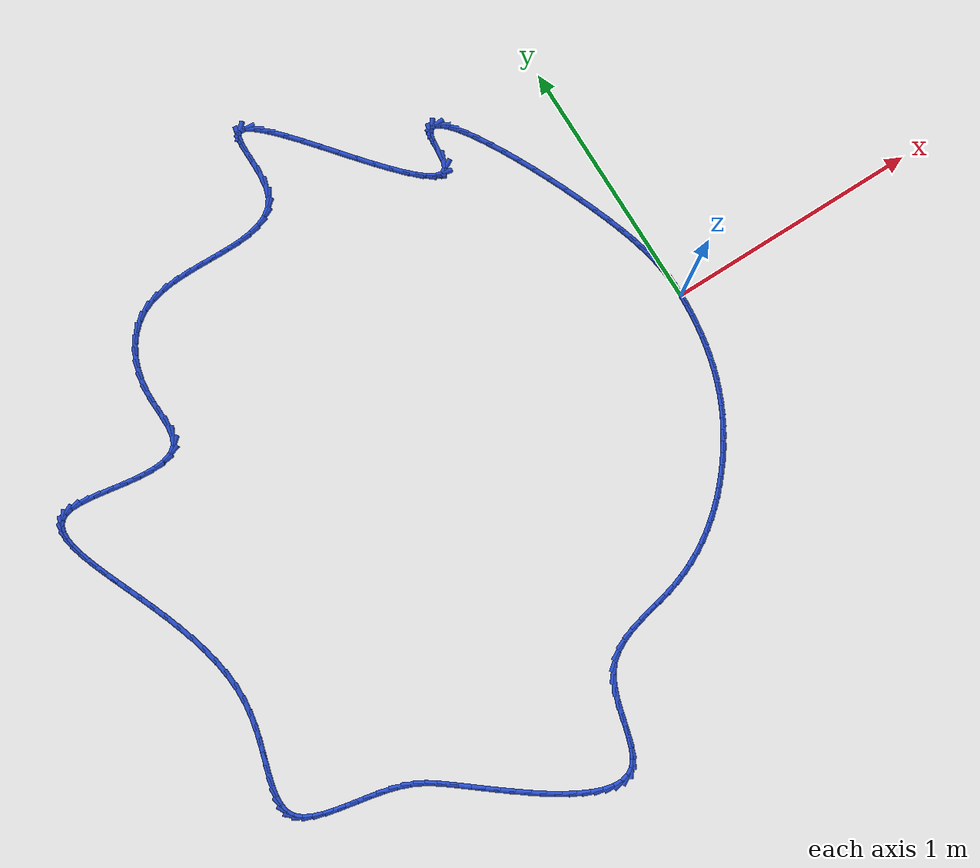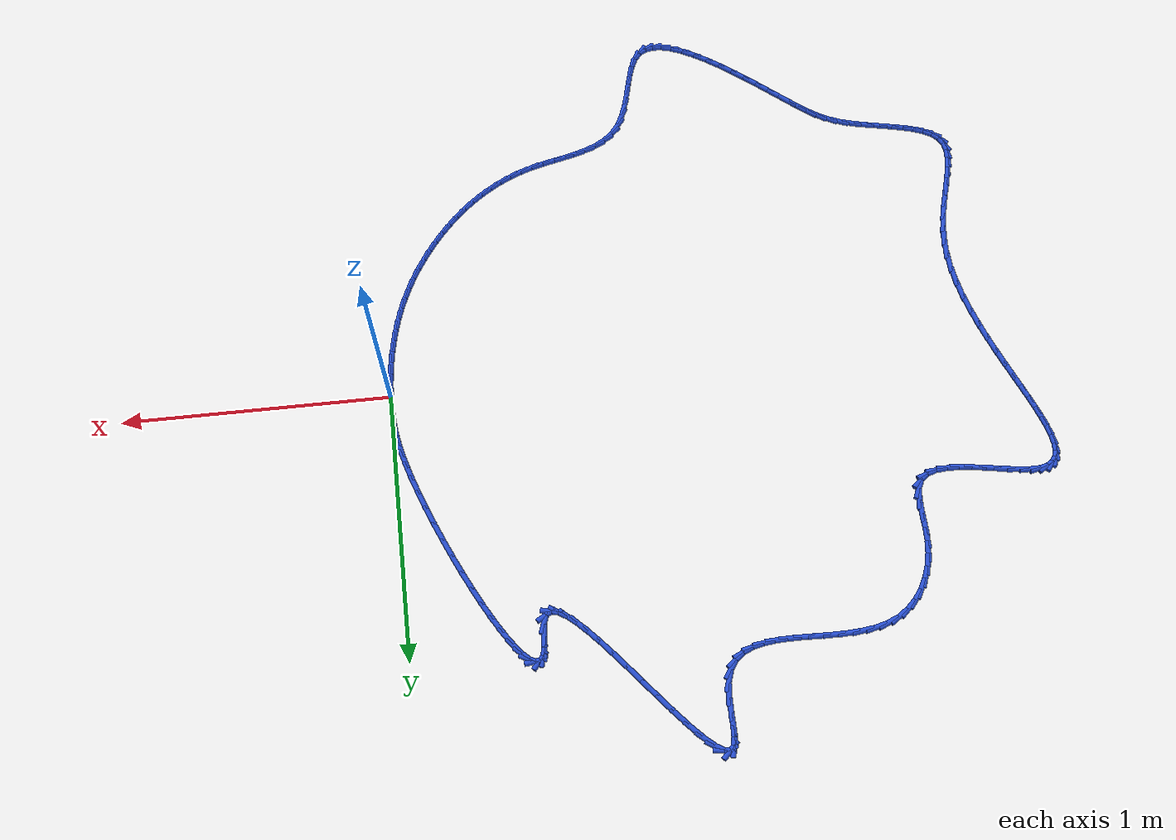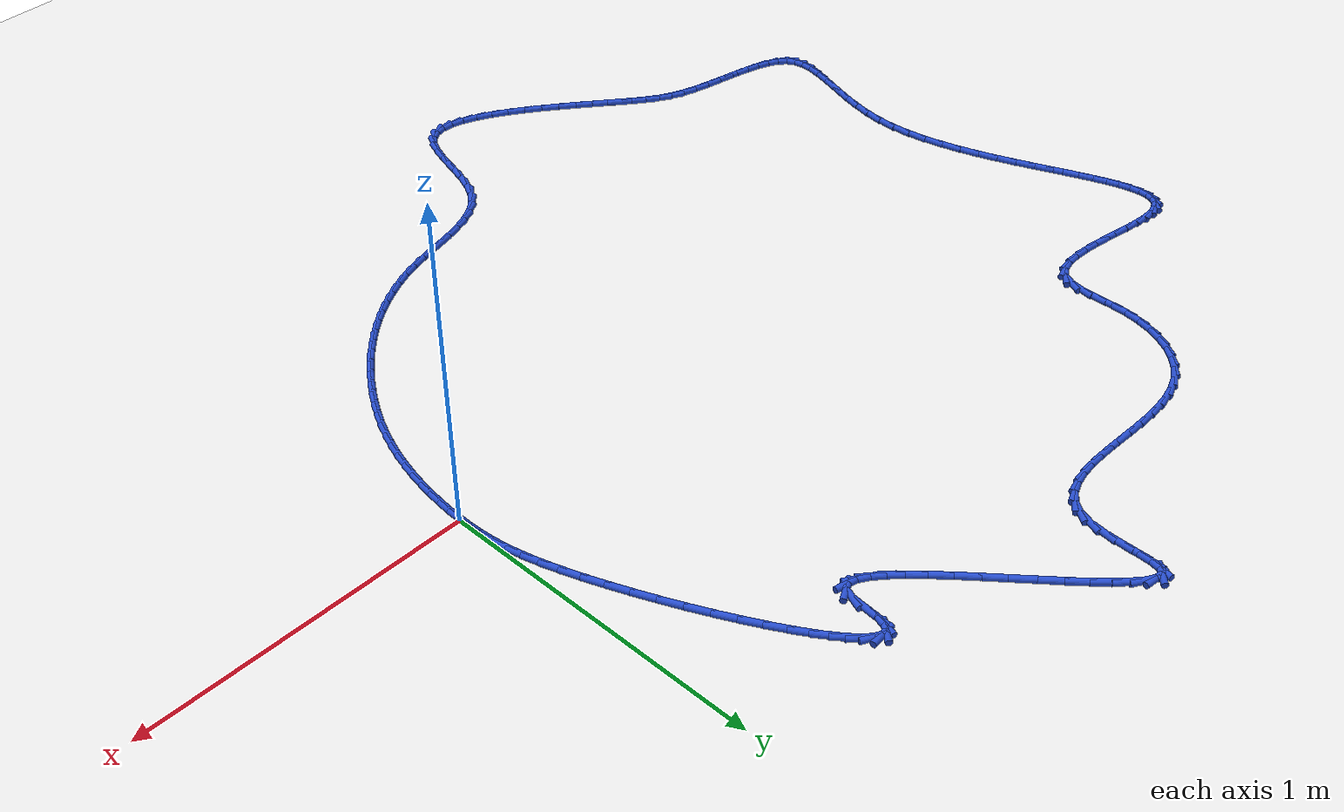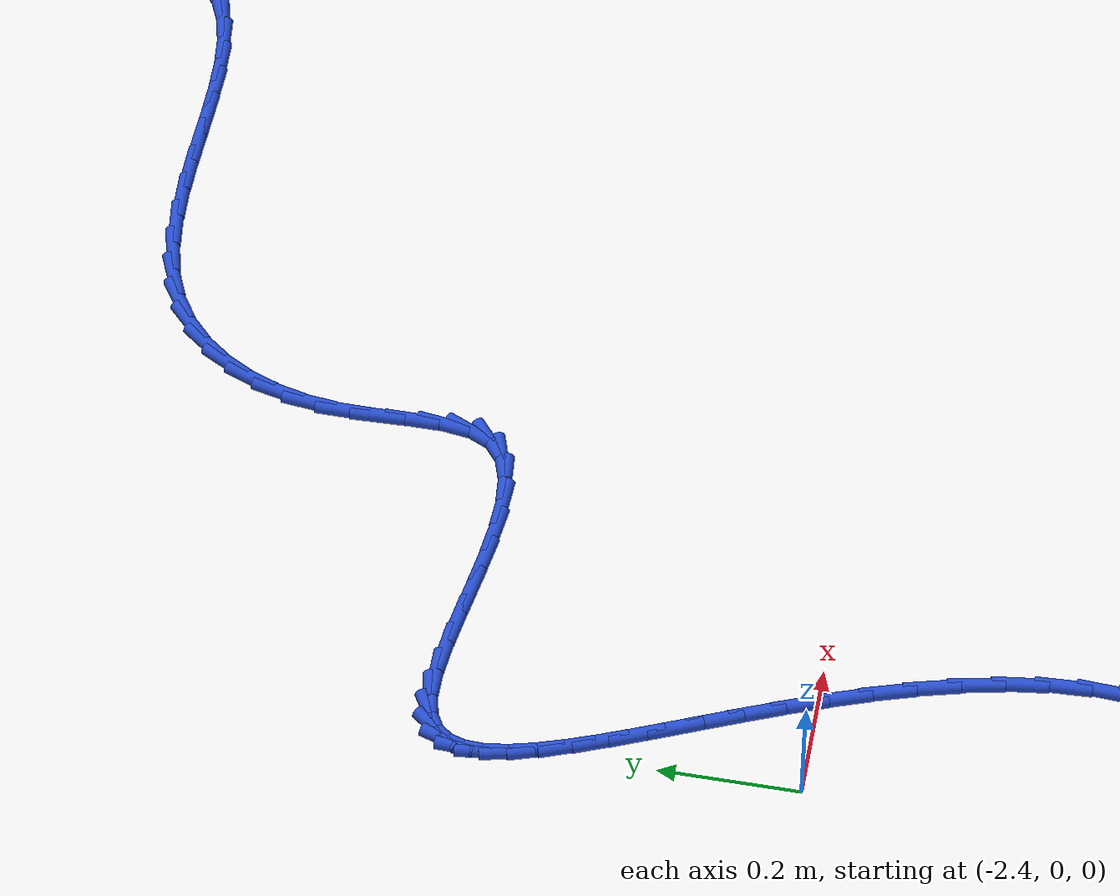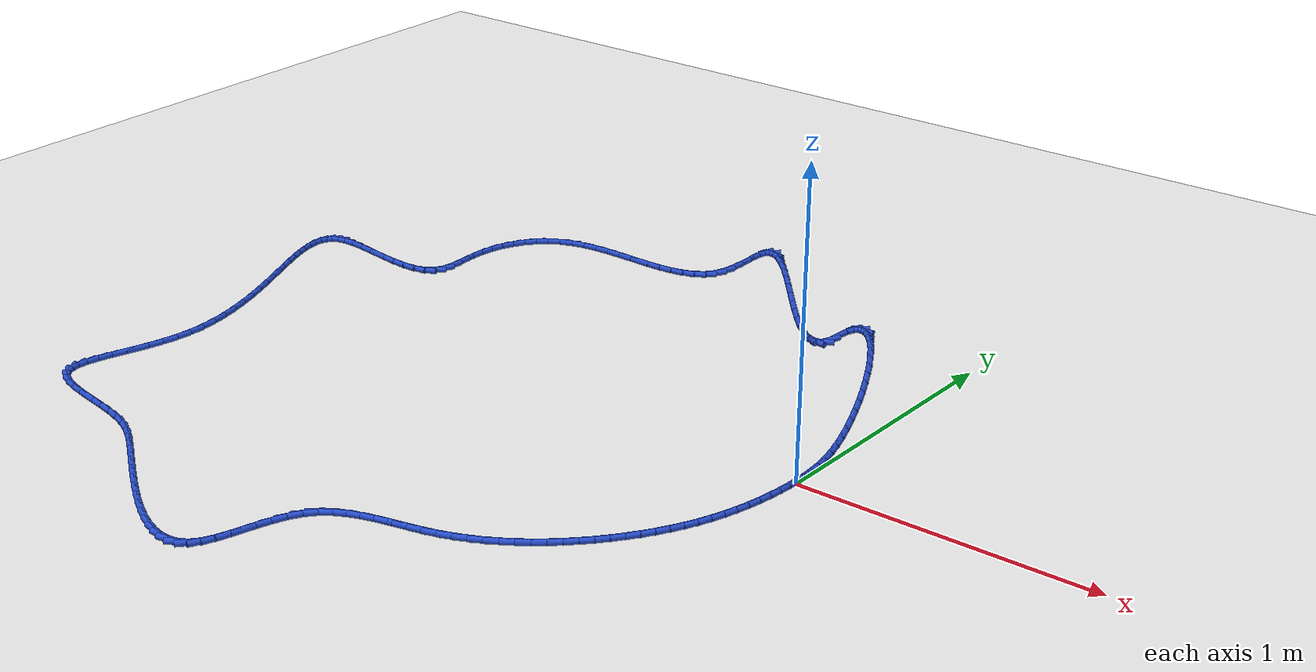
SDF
<sdf version="1.6">
 <world name="default">
  <light name="sun" type="directional">
   <pose>0 0 10 0 -0 0</pose>
   <diffuse>0.8 0.8 0.8 1</diffuse>
   <specular>0.2 0.2 0.2 1</specular>
   <attenuation>
    <range>1000</range>
    <constant>0.9</constant>
    <linear>0.01</linear>
    <quadratic>0.001</quadratic>
   </attenuation>
   <direction>-0.5 0.1 -0.9</direction>
  </light>
  <model name="ground_plane">
   <static>1</static>
   <link name="link">
    <collision name="collision">
     <geometry><plane><normal>0 0 1</normal><size>100 100</size></plane></geometry>
     <surface><friction><ode><mu>100</mu><mu2>50</mu2></ode></friction></surface>
    </collision>
    <visual name="visual">
     <cast_shadows>0</cast_shadows>
     <geometry><plane><normal>0 0 1</normal><size>100 100</size></plane></geometry>
     <material>
      <script><uri>file://media/materials/scripts/gazebo.material</uri><name>Gazebo/WhiteGlow</name></script>
     </material>
    </visual>
   </link>
  </model>
  <gravity>0 0 -9.8</gravity>
  <magnetic_field>6e-06 2.3e-05 -4.2e-05</magnetic_field>
  <atmosphere type="adiabatic"/>
  <physics name="default_physics" default="0" type="ode">
   <max_step_size>0.001</max_step_size>
   <real_time_factor>1</real_time_factor>
   <real_time_update_rate>1000</real_time_update_rate>
  </physics>
  <scene><ambient>0.4 0.4 0.4 1</ambient><background>0.7 0.7 0.7 1</background><shadows>1</shadows></scene>
  <spherical_coordinates>
   <surface_model>EARTH_WGS84</surface_model>
   <latitude_deg>0</latitude_deg>
   <longitude_deg>0</longitude_deg>
   <elevation>0</elevation>
   <heading_deg>0</heading_deg>
  </spherical_coordinates>
  <model name="line">
   <link name="link_0">
    <pose>3.642919299551295e-17 -1.249000902703301e-16 0.01 0 1.57 1.5675305549018665</pose>
    <collision name="collision">
     <geometry><cylinder><radius>0.01</radius><length>0.08</length></cylinder></geometry>
    </collision>
    <visual name="visual">
     <material>
      <script><name>Gazebo/Blue</name><uri>file://media/materials/scripts/gazebo.material</uri></script>
     </material>
     <geometry><cylinder><radius>0.01</radius><length>0.08</length></cylinder></geometry>
    </visual>
   </link>
   <link name="link_1">
    <pose>0.00013204881284345442 0.040434037563880275 0.01 0 1.57 -1.5289638000909016</pose>
    <collision name="collision">
     <geometry><cylinder><radius>0.01</radius><length>0.08</length></cylinder></geometry>
    </collision>
    <visual name="visual">
     <material>
      <script><name>Gazebo/Blue</name><uri>file://media/materials/scripts/gazebo.material</uri></script>
     </material>
     <geometry><cylinder><radius>0.01</radius><length>0.08</length></cylinder></geometry>
    </visual>
   </link>
   <link name="link_2">
    <pose>-0.0015336639610331732 0.08022941087577645 0.01 0 1.57 -1.4778730629713173</pose>
    <collision name="collision">
     <geometry><cylinder><radius>0.01</radius><length>0.08</length></cylinder></geometry>
    </collision>
    <visual name="visual">
     <material>
      <script><name>Gazebo/Blue</name><uri>file://media/materials/scripts/gazebo.material</uri></script>
     </material>
     <geometry><cylinder><radius>0.01</radius><length>0.08</length></cylinder></geometry>
    </visual>
   </link>
   <link name="link_3">
    <pose>-0.0052633257673743595 0.12025082844981046 0.01 0 1.57 -1.4244533599746951</pose>
    <collision name="collision">
     <geometry><cylinder><radius>0.01</radius><length>0.08</length></cylinder></geometry>
    </collision>
    <visual name="visual">
     <material>
      <script><name>Gazebo/Blue</name><uri>file://media/materials/scripts/gazebo.material</uri></script>
     </material>
     <geometry><cylinder><radius>0.01</radius><length>0.08</length></cylinder></geometry>
    </visual>
   </link>
   <link name="link_4">
    <pose>-0.011323124051924623 0.1613629988001043 0.01 0 1.57 -1.372449942052213</pose>
    <collision name="collision">
     <geometry><cylinder><radius>0.01</radius><length>0.08</length></cylinder></geometry>
    </collision>
    <visual name="visual">
     <material>
      <script><name>Gazebo/Blue</name><uri>file://media/materials/scripts/gazebo.material</uri></script>
     </material>
     <geometry><cylinder><radius>0.01</radius><length>0.08</length></cylinder></geometry>
    </visual>
   </link>
   <link name="link_5">
    <pose>-0.019979246260428477 0.20443063044077986 0.01 0 1.57 -1.3248604023548292</pose>
    <collision name="collision">
     <geometry><cylinder><radius>0.01</radius><length>0.08</length></cylinder></geometry>
    </collision>
    <visual name="visual">
     <material>
      <script><name>Gazebo/Blue</name><uri>file://media/materials/scripts/gazebo.material</uri></script>
     </material>
     <geometry><cylinder><radius>0.01</radius><length>0.08</length></cylinder></geometry>
    </visual>
   </link>
   <link name="link_6">
    <pose>-0.03149787983863044 0.25031843188595915 0.01 0 1.57 -1.2834989397748582</pose>
    <collision name="collision">
     <geometry><cylinder><radius>0.01</radius><length>0.08</length></cylinder></geometry>
    </collision>
    <visual name="visual">
     <material>
      <script><name>Gazebo/Blue</name><uri>file://media/materials/scripts/gazebo.material</uri></script>
     </material>
     <geometry><cylinder><radius>0.01</radius><length>0.08</length></cylinder></geometry>
    </visual>
   </link>
   <link name="link_7">
    <pose>-0.04614521223227501 0.2998911116497641 0.01 0 1.57 -1.2490533181175454</pose>
    <collision name="collision">
     <geometry><cylinder><radius>0.01</radius><length>0.08</length></cylinder></geometry>
    </collision>
    <visual name="visual">
     <material>
      <script><name>Gazebo/Blue</name><uri>file://media/materials/scripts/gazebo.material</uri></script>
     </material>
     <geometry><cylinder><radius>0.01</radius><length>0.08</length></cylinder></geometry>
    </visual>
   </link>
   <link name="link_8">
    <pose>-0.06416881593541561 0.353963282800515 0.01 0 1.57 -1.2213529962305636</pose>
    <collision name="collision">
     <geometry><cylinder><radius>0.01</radius><length>0.08</length></cylinder></geometry>
    </collision>
    <visual name="visual">
     <material>
      <script><name>Gazebo/Blue</name><uri>file://media/materials/scripts/gazebo.material</uri></script>
     </material>
     <geometry><cylinder><radius>0.01</radius><length>0.08</length></cylinder></geometry>
    </visual>
   </link>
   <link name="link_9">
    <pose>-0.0854431952737523 0.41234557964160035 0.01 0 1.57 -1.198368762805631</pose>
    <collision name="collision">
     <geometry><cylinder><radius>0.01</radius><length>0.08</length></cylinder></geometry>
    </collision>
    <visual name="visual">
     <material>
      <script><name>Gazebo/Blue</name><uri>file://media/materials/scripts/gazebo.material</uri></script>
     </material>
     <geometry><cylinder><radius>0.01</radius><length>0.08</length></cylinder></geometry>
    </visual>
   </link>
   <link name="link_10">
    <pose>-0.10949803848147606 0.47392068801270076 0.01 0 1.57 -1.1780766225657335</pose>
    <collision name="collision">
     <geometry><cylinder><radius>0.01</radius><length>0.08</length></cylinder></geometry>
    </collision>
    <visual name="visual">
     <material>
      <script><name>Gazebo/Blue</name><uri>file://media/materials/scripts/gazebo.material</uri></script>
     </material>
     <geometry><cylinder><radius>0.01</radius><length>0.08</length></cylinder></geometry>
    </visual>
   </link>
   <link name="link_11">
    <pose>-0.13585008024350254 0.5375364339356239 0.01 0 1.57 -1.15909679112549</pose>
    <collision name="collision">
     <geometry><cylinder><radius>0.01</radius><length>0.08</length></cylinder></geometry>
    </collision>
    <visual name="visual">
     <material>
      <script><name>Gazebo/Blue</name><uri>file://media/materials/scripts/gazebo.material</uri></script>
     </material>
     <geometry><cylinder><radius>0.01</radius><length>0.08</length></cylinder></geometry>
    </visual>
   </link>
   <link name="link_12">
    <pose>-0.16401605524474738 0.6020406434321773 0.01 0 1.57 -1.1403514220026696</pose>
    <collision name="collision">
     <geometry><cylinder><radius>0.01</radius><length>0.08</length></cylinder></geometry>
    </collision>
    <visual name="visual">
     <material>
      <script><name>Gazebo/Blue</name><uri>file://media/materials/scripts/gazebo.material</uri></script>
     </material>
     <geometry><cylinder><radius>0.01</radius><length>0.08</length></cylinder></geometry>
    </visual>
   </link>
   <link name="link_13">
    <pose>-0.19351269817012612 0.6662811425241687 0.01 0 1.57 -1.1208441162725937</pose>
    <collision name="collision">
     <geometry><cylinder><radius>0.01</radius><length>0.08</length></cylinder></geometry>
    </collision>
    <visual name="visual">
     <material>
      <script><name>Gazebo/Blue</name><uri>file://media/materials/scripts/gazebo.material</uri></script>
     </material>
     <geometry><cylinder><radius>0.01</radius><length>0.08</length></cylinder></geometry>
    </visual>
   </link>
   <link name="link_14">
    <pose>-0.22385674370455444 0.729105757233406 0.01 0 1.57 -1.0994792519023115</pose>
    <collision name="collision">
     <geometry><cylinder><radius>0.01</radius><length>0.08</length></cylinder></geometry>
    </collision>
    <visual name="visual">
     <material>
      <script><name>Gazebo/Blue</name><uri>file://media/materials/scripts/gazebo.material</uri></script>
     </material>
     <geometry><cylinder><radius>0.01</radius><length>0.08</length></cylinder></geometry>
    </visual>
   </link>
   <link name="link_15">
    <pose>-0.25456492653294804 0.7893623135816967 0.01 0 1.57 -1.0748494255696108</pose>
    <collision name="collision">
     <geometry><cylinder><radius>0.01</radius><length>0.08</length></cylinder></geometry>
    </collision>
    <visual name="visual">
     <material>
      <script><name>Gazebo/Blue</name><uri>file://media/materials/scripts/gazebo.material</uri></script>
     </material>
     <geometry><cylinder><radius>0.01</radius><length>0.08</length></cylinder></geometry>
    </visual>
   </link>
   <link name="link_16">
    <pose>-0.2851539813402225 0.8458986375908486 0.01 0 1.57 -1.0448999007071222</pose>
    <collision name="collision">
     <geometry><cylinder><radius>0.01</radius><length>0.08</length></cylinder></geometry>
    </collision>
    <visual name="visual">
     <material>
      <script><name>Gazebo/Blue</name><uri>file://media/materials/scripts/gazebo.material</uri></script>
     </material>
     <geometry><cylinder><radius>0.01</radius><length>0.08</length></cylinder></geometry>
    </visual>
   </link>
   <link name="link_17">
    <pose>-0.3151406428112934 0.8975625552826689 0.01 0 1.57 -1.0062880945647572</pose>
    <collision name="collision">
     <geometry><cylinder><radius>0.01</radius><length>0.08</length></cylinder></geometry>
    </collision>
    <visual name="visual">
     <material>
      <script><name>Gazebo/Blue</name><uri>file://media/materials/scripts/gazebo.material</uri></script>
     </material>
     <geometry><cylinder><radius>0.01</radius><length>0.08</length></cylinder></geometry>
    </visual>
   </link>
   <link name="link_18">
    <pose>-0.3440416456310764 0.9432018926789661 0.01 0 1.57 -0.9529818380928203</pose>
    <collision name="collision">
     <geometry><cylinder><radius>0.01</radius><length>0.08</length></cylinder></geometry>
    </collision>
    <visual name="visual">
     <material>
      <script><name>Gazebo/Blue</name><uri>file://media/materials/scripts/gazebo.material</uri></script>
     </material>
     <geometry><cylinder><radius>0.01</radius><length>0.08</length></cylinder></geometry>
    </visual>
   </link>
   <link name="link_19">
    <pose>-0.3713737244844871 0.981664475801547 0.01 0 1.57 -0.8727668562768829</pose>
    <collision name="collision">
     <geometry><cylinder><radius>0.01</radius><length>0.08</length></cylinder></geometry>
    </collision>
    <visual name="visual">
     <material>
      <script><name>Gazebo/Blue</name><uri>file://media/materials/scripts/gazebo.material</uri></script>
     </material>
     <geometry><cylinder><radius>0.01</radius><length>0.08</length></cylinder></geometry>
    </visual>
   </link>
   <link name="link_20">
    <pose>-0.3966536140564412 1.0117981306722204 0.01 0 1.57 -0.7372320464701948</pose>
    <collision name="collision">
     <geometry><cylinder><radius>0.01</radius><length>0.08</length></cylinder></geometry>
    </collision>
    <visual name="visual">
     <material>
      <script><name>Gazebo/Blue</name><uri>file://media/materials/scripts/gazebo.material</uri></script>
     </material>
     <geometry><cylinder><radius>0.01</radius><length>0.08</length></cylinder></geometry>
    </visual>
   </link>
   <link name="link_21">
    <pose>-0.4193980490318544 1.0324506833127929 0.01 0 1.57 -0.4699712225609622</pose>
    <collision name="collision">
     <geometry><cylinder><radius>0.01</radius><length>0.08</length></cylinder></geometry>
    </collision>
    <visual name="visual">
     <material>
      <script><name>Gazebo/Blue</name><uri>file://media/materials/scripts/gazebo.material</uri></script>
     </material>
     <geometry><cylinder><radius>0.01</radius><length>0.08</length></cylinder></geometry>
    </visual>
   </link>
   <link name="link_22">
    <pose>-0.43912376409564224 1.0424699597450728 0.01 0 1.57 0.10843658183100048</pose>
    <collision name="collision">
     <geometry><cylinder><radius>0.01</radius><length>0.08</length></cylinder></geometry>
    </collision>
    <visual name="visual">
     <material>
      <script><name>Gazebo/Blue</name><uri>file://media/materials/scripts/gazebo.material</uri></script>
     </material>
     <geometry><cylinder><radius>0.01</radius><length>0.08</length></cylinder></geometry>
    </visual>
   </link>
   <link name="link_23">
    <pose>-0.4553474939327202 1.0407037859908674 0.01 0 1.57 0.8766477752174875</pose>
    <collision name="collision">
     <geometry><cylinder><radius>0.01</radius><length>0.08</length></cylinder></geometry>
    </collision>
    <visual name="visual">
     <material>
      <script><name>Gazebo/Blue</name><uri>file://media/materials/scripts/gazebo.material</uri></script>
     </material>
     <geometry><cylinder><radius>0.01</radius><length>0.08</length></cylinder></geometry>
    </visual>
   </link>
   <link name="link_24">
    <pose>-0.46758597322800416 1.0259999880719848 0.01 0 1.57 1.3072239319896677</pose>
    <collision name="collision">
     <geometry><cylinder><radius>0.01</radius><length>0.08</length></cylinder></geometry>
    </collision>
    <visual name="visual">
     <material>
      <script><name>Gazebo/Blue</name><uri>file://media/materials/scripts/gazebo.material</uri></script>
     </material>
     <geometry><cylinder><radius>0.01</radius><length>0.08</length></cylinder></geometry>
    </visual>
   </link>
   <link name="link_25">
    <pose>-0.47535593666640963 0.9972063920102325 0.01 0 1.57 1.4933248266433363</pose>
    <collision name="collision">
     <geometry><cylinder><radius>0.01</radius><length>0.08</length></cylinder></geometry>
    </collision>
    <visual name="visual">
     <material>
      <script><name>Gazebo/Blue</name><uri>file://media/materials/scripts/gazebo.material</uri></script>
     </material>
     <geometry><cylinder><radius>0.01</radius><length>0.08</length></cylinder></geometry>
    </visual>
   </link>
   <link name="link_26">
    <pose>-0.4786744924310509 0.9544562973220283 0.01 0 1.57 1.485703215350793</pose>
    <collision name="collision">
     <geometry><cylinder><radius>0.01</radius><length>0.08</length></cylinder></geometry>
    </collision>
    <visual name="visual">
     <material>
      <script><name>Gazebo/Blue</name><uri>file://media/materials/scripts/gazebo.material</uri></script>
     </material>
     <geometry><cylinder><radius>0.01</radius><length>0.08</length></cylinder></geometry>
    </visual>
   </link>
   <link name="link_27">
    <pose>-0.48243219632802725 0.9104030266050909 0.01 0 1.57 1.2114208996746536</pose>
    <collision name="collision">
     <geometry><cylinder><radius>0.01</radius><length>0.08</length></cylinder></geometry>
    </collision>
    <visual name="visual">
     <material>
      <script><name>Gazebo/Blue</name><uri>file://media/materials/scripts/gazebo.material</uri></script>
     </material>
     <geometry><cylinder><radius>0.01</radius><length>0.08</length></cylinder></geometry>
    </visual>
   </link>
   <link name="link_28">
    <pose>-0.4931418167845878 0.8818964875097275 0.01 0 1.57 0.5169518094988509</pose>
    <collision name="collision">
     <geometry><cylinder><radius>0.01</radius><length>0.08</length></cylinder></geometry>
    </collision>
    <visual name="visual">
     <material>
      <script><name>Gazebo/Blue</name><uri>file://media/materials/scripts/gazebo.material</uri></script>
     </material>
     <geometry><cylinder><radius>0.01</radius><length>0.08</length></cylinder></geometry>
    </visual>
   </link>
   <link name="link_29">
    <pose>-0.511648975754148 0.8713747715895243 0.01 0 1.57 -0.20703830014768174</pose>
    <collision name="collision">
     <geometry><cylinder><radius>0.01</radius><length>0.08</length></cylinder></geometry>
    </collision>
    <visual name="visual">
     <material>
      <script><name>Gazebo/Blue</name><uri>file://media/materials/scripts/gazebo.material</uri></script>
     </material>
     <geometry><cylinder><radius>0.01</radius><length>0.08</length></cylinder></geometry>
    </visual>
   </link>
   <link name="link_30">
    <pose>-0.536999863244989 0.8766996783458426 0.01 0 1.57 -0.5471589298171924</pose>
    <collision name="collision">
     <geometry><cylinder><radius>0.01</radius><length>0.08</length></cylinder></geometry>
    </collision>
    <visual name="visual">
     <material>
      <script><name>Gazebo/Blue</name><uri>file://media/materials/scripts/gazebo.material</uri></script>
     </material>
     <geometry><cylinder><radius>0.01</radius><length>0.08</length></cylinder></geometry>
    </visual>
   </link>
   <link name="link_31">
    <pose>-0.5682399780000161 0.8957312492628782 0.01 0 1.57 -0.7020764117601845</pose>
    <collision name="collision">
     <geometry><cylinder><radius>0.01</radius><length>0.08</length></cylinder></geometry>
    </collision>
    <visual name="visual">
     <material>
      <script><name>Gazebo/Blue</name><uri>file://media/materials/scripts/gazebo.material</uri></script>
     </material>
     <geometry><cylinder><radius>0.01</radius><length>0.08</length></cylinder></geometry>
    </visual>
   </link>
   <link name="link_32">
    <pose>-0.6044148187621342 0.9263295258248273 0.01 0 1.57 -0.7837762930762134</pose>
    <collision name="collision">
     <geometry><cylinder><radius>0.01</radius><length>0.08</length></cylinder></geometry>
    </collision>
    <visual name="visual">
     <material>
      <script><name>Gazebo/Blue</name><uri>file://media/materials/scripts/gazebo.material</uri></script>
     </material>
     <geometry><cylinder><radius>0.01</radius><length>0.08</length></cylinder></geometry>
    </visual>
   </link>
   <link name="link_33">
    <pose>-0.6445698842742482 0.9663545495158853 0.01 0 1.57 -0.8310168901755962</pose>
    <collision name="collision">
     <geometry><cylinder><radius>0.01</radius><length>0.08</length></cylinder></geometry>
    </collision>
    <visual name="visual">
     <material>
      <script><name>Gazebo/Blue</name><uri>file://media/materials/scripts/gazebo.material</uri></script>
     </material>
     <geometry><cylinder><radius>0.01</radius><length>0.08</length></cylinder></geometry>
    </visual>
   </link>
   <link name="link_34">
    <pose>-0.6877506732792638 1.013666361820249 0.01 0 1.57 -0.8590196765059893</pose>
    <collision name="collision">
     <geometry><cylinder><radius>0.01</radius><length>0.08</length></cylinder></geometry>
    </collision>
    <visual name="visual">
     <material>
      <script><name>Gazebo/Blue</name><uri>file://media/materials/scripts/gazebo.material</uri></script>
     </material>
     <geometry><cylinder><radius>0.01</radius><length>0.08</length></cylinder></geometry>
    </visual>
   </link>
   <link name="link_35">
    <pose>-0.7330026845200852 1.0661250042221138 0.01 0 1.57 -0.8744909852540778</pose>
    <collision name="collision">
     <geometry><cylinder><radius>0.01</radius><length>0.08</length></cylinder></geometry>
    </collision>
    <visual name="visual">
     <material>
      <script><name>Gazebo/Blue</name><uri>file://media/materials/scripts/gazebo.material</uri></script>
     </material>
     <geometry><cylinder><radius>0.01</radius><length>0.08</length></cylinder></geometry>
    </visual>
   </link>
   <link name="link_36">
    <pose>-0.779371416739618 1.1215905182056756 0.01 0 1.57 -0.880397682591447</pose>
    <collision name="collision">
     <geometry><cylinder><radius>0.01</radius><length>0.08</length></cylinder></geometry>
    </collision>
    <visual name="visual">
     <material>
      <script><name>Gazebo/Blue</name><uri>file://media/materials/scripts/gazebo.material</uri></script>
     </material>
     <geometry><cylinder><radius>0.01</radius><length>0.08</length></cylinder></geometry>
    </visual>
   </link>
   <link name="link_37">
    <pose>-0.825902368680767 1.1779229452551307 0.01 0 1.57 -0.8776051133441326</pose>
    <collision name="collision">
     <geometry><cylinder><radius>0.01</radius><length>0.08</length></cylinder></geometry>
    </collision>
    <visual name="visual">
     <material>
      <script><name>Gazebo/Blue</name><uri>file://media/materials/scripts/gazebo.material</uri></script>
     </material>
     <geometry><cylinder><radius>0.01</radius><length>0.08</length></cylinder></geometry>
    </visual>
   </link>
   <link name="link_38">
    <pose>-0.8716410390864374 1.2329823268546745 0.01 0 1.57 -0.8652637727848173</pose>
    <collision name="collision">
     <geometry><cylinder><radius>0.01</radius><length>0.08</length></cylinder></geometry>
    </collision>
    <visual name="visual">
     <material>
      <script><name>Gazebo/Blue</name><uri>file://media/materials/scripts/gazebo.material</uri></script>
     </material>
     <geometry><cylinder><radius>0.01</radius><length>0.08</length></cylinder></geometry>
    </visual>
   </link>
   <link name="link_39">
    <pose>-0.9156329266995347 1.2846287044885039 0.01 0 1.57 -0.8403050472672351</pose>
    <collision name="collision">
     <geometry><cylinder><radius>0.01</radius><length>0.08</length></cylinder></geometry>
    </collision>
    <visual name="visual">
     <material>
      <script><name>Gazebo/Blue</name><uri>file://media/materials/scripts/gazebo.material</uri></script>
     </material>
     <geometry><cylinder><radius>0.01</radius><length>0.08</length></cylinder></geometry>
    </visual>
   </link>
   <link name="link_40">
    <pose>-0.9569235302629632 1.330722119640814 0.01 0 1.57 -0.7954678270115721</pose>
    <collision name="collision">
     <geometry><cylinder><radius>0.01</radius><length>0.08</length></cylinder></geometry>
    </collision>
    <visual name="visual">
     <material>
      <script><name>Gazebo/Blue</name><uri>file://media/materials/scripts/gazebo.material</uri></script>
     </material>
     <geometry><cylinder><radius>0.01</radius><length>0.08</length></cylinder></geometry>
    </visual>
   </link>
   <link name="link_41">
    <pose>-0.9945583485196283 1.3691226137958012 0.01 0 1.57 -0.7131622936921519</pose>
    <collision name="collision">
     <geometry><cylinder><radius>0.01</radius><length>0.08</length></cylinder></geometry>
    </collision>
    <visual name="visual">
     <material>
      <script><name>Gazebo/Blue</name><uri>file://media/materials/scripts/gazebo.material</uri></script>
     </material>
     <geometry><cylinder><radius>0.01</radius><length>0.08</length></cylinder></geometry>
    </visual>
   </link>
   <link name="link_42">
    <pose>-1.0275828802124352 1.3976902284376613 0.01 0 1.57 -0.5435980322061625</pose>
    <collision name="collision">
     <geometry><cylinder><radius>0.01</radius><length>0.08</length></cylinder></geometry>
    </collision>
    <visual name="visual">
     <material>
      <script><name>Gazebo/Blue</name><uri>file://media/materials/scripts/gazebo.material</uri></script>
     </material>
     <geometry><cylinder><radius>0.01</radius><length>0.08</length></cylinder></geometry>
    </visual>
   </link>
   <link name="link_43">
    <pose>-1.0550426240842887 1.4142850050505902 0.01 0 1.57 -0.11797520814265441</pose>
    <collision name="collision">
     <geometry><cylinder><radius>0.01</radius><length>0.08</length></cylinder></geometry>
    </collision>
    <visual name="visual">
     <material>
      <script><name>Gazebo/Blue</name><uri>file://media/materials/scripts/gazebo.material</uri></script>
     </material>
     <geometry><cylinder><radius>0.01</radius><length>0.08</length></cylinder></geometry>
    </visual>
   </link>
   <link name="link_44">
    <pose>-1.0759830788780942 1.416766985118784 0.01 0 1.57 0.7964009535426912</pose>
    <collision name="collision">
     <geometry><cylinder><radius>0.01</radius><length>0.08</length></cylinder></geometry>
    </collision>
    <visual name="visual">
     <material>
      <script><name>Gazebo/Blue</name><uri>file://media/materials/scripts/gazebo.material</uri></script>
     </material>
     <geometry><cylinder><radius>0.01</radius><length>0.08</length></cylinder></geometry>
    </visual>
   </link>
   <link name="link_45">
    <pose>-1.0894513312730991 1.4029990465365274 0.01 0 1.57 1.3750329016965717</pose>
    <collision name="collision">
     <geometry><cylinder><radius>0.01</radius><length>0.08</length></cylinder></geometry>
    </collision>
    <visual name="visual">
     <material>
      <script><name>Gazebo/Blue</name><uri>file://media/materials/scripts/gazebo.material</uri></script>
     </material>
     <geometry><cylinder><radius>0.01</radius><length>0.08</length></cylinder></geometry>
    </visual>
   </link>
   <link name="link_46">
    <pose>-1.0954790218061357 1.3726027009796384 0.01 0 1.57 1.5407870323351818</pose>
    <collision name="collision">
     <geometry><cylinder><radius>0.01</radius><length>0.08</length></cylinder></geometry>
    </collision>
    <visual name="visual">
     <material>
      <script><name>Gazebo/Blue</name><uri>file://media/materials/scripts/gazebo.material</uri></script>
     </material>
     <geometry><cylinder><radius>0.01</radius><length>0.08</length></cylinder></geometry>
    </visual>
   </link>
   <link name="link_47">
    <pose>-1.096759279337885 1.3299534745837982 0.01 0 1.57 -1.5641857784162334</pose>
    <collision name="collision">
     <geometry><cylinder><radius>0.01</radius><length>0.08</length></cylinder></geometry>
    </collision>
    <visual name="visual">
     <material>
      <script><name>Gazebo/Blue</name><uri>file://media/materials/scripts/gazebo.material</uri></script>
     </material>
     <geometry><cylinder><radius>0.01</radius><length>0.08</length></cylinder></geometry>
    </visual>
   </link>
   <link name="link_48">
    <pose>-1.0964305241054897 1.2802222836517556 0.01 0 1.57 1.5475510919182662</pose>
    <collision name="collision">
     <geometry><cylinder><radius>0.01</radius><length>0.08</length></cylinder></geometry>
    </collision>
    <visual name="visual">
     <material>
      <script><name>Gazebo/Blue</name><uri>file://media/materials/scripts/gazebo.material</uri></script>
     </material>
     <geometry><cylinder><radius>0.01</radius><length>0.08</length></cylinder></geometry>
    </visual>
   </link>
   <link name="link_49">
    <pose>-1.0976311763460924 1.2285800444862605 0.01 0 1.57 1.4500921973668244</pose>
    <collision name="collision">
     <geometry><cylinder><radius>0.01</radius><length>0.08</length></cylinder></geometry>
    </collision>
    <visual name="visual">
     <material>
      <script><name>Gazebo/Blue</name><uri>file://media/materials/scripts/gazebo.material</uri></script>
     </material>
     <geometry><cylinder><radius>0.01</radius><length>0.08</length></cylinder></geometry>
    </visual>
   </link>
   <link name="link_50">
    <pose>-1.1034996562968362 1.1801976733900603 0.01 0 1.57 1.247685210929813</pose>
    <collision name="collision">
     <geometry><cylinder><radius>0.01</radius><length>0.08</length></cylinder></geometry>
    </collision>
    <visual name="visual">
     <material>
      <script><name>Gazebo/Blue</name><uri>file://media/materials/scripts/gazebo.material</uri></script>
     </material>
     <geometry><cylinder><radius>0.01</radius><length>0.08</length></cylinder></geometry>
    </visual>
   </link>
   <link name="link_51">
    <pose>-1.116979054578009 1.1399421286384048 0.01 0 1.57 0.9585325866514751</pose>
    <collision name="collision">
     <geometry><cylinder><radius>0.01</radius><length>0.08</length></cylinder></geometry>
    </collision>
    <visual name="visual">
     <material>
      <script><name>Gazebo/Blue</name><uri>file://media/materials/scripts/gazebo.material</uri></script>
     </material>
     <geometry><cylinder><radius>0.01</radius><length>0.08</length></cylinder></geometry>
    </visual>
   </link>
   <link name="link_52">
    <pose>-1.1386770717271772 1.1090462009163031 0.01 0 1.57 0.6643002942133427</pose>
    <collision name="collision">
     <geometry><cylinder><radius>0.01</radius><length>0.08</length></cylinder></geometry>
    </collision>
    <visual name="visual">
     <material>
      <script><name>Gazebo/Blue</name><uri>file://media/materials/scripts/gazebo.material</uri></script>
     </material>
     <geometry><cylinder><radius>0.01</radius><length>0.08</length></cylinder></geometry>
    </visual>
   </link>
   <link name="link_53">
    <pose>-1.167663411075158 1.0863493592774023 0.01 0 1.57 0.4183153253839914</pose>
    <collision name="collision">
     <geometry><cylinder><radius>0.01</radius><length>0.08</length></cylinder></geometry>
    </collision>
    <visual name="visual">
     <material>
      <script><name>Gazebo/Blue</name><uri>file://media/materials/scripts/gazebo.material</uri></script>
     </material>
     <geometry><cylinder><radius>0.01</radius><length>0.08</length></cylinder></geometry>
    </visual>
   </link>
   <link name="link_54">
    <pose>-1.2029806993120946 1.0706489380370365 0.01 0 1.57 0.23881555728746684</pose>
    <collision name="collision">
     <geometry><cylinder><radius>0.01</radius><length>0.08</length></cylinder></geometry>
    </collision>
    <visual name="visual">
     <material>
      <script><name>Gazebo/Blue</name><uri>file://media/materials/scripts/gazebo.material</uri></script>
     </material>
     <geometry><cylinder><radius>0.01</radius><length>0.08</length></cylinder></geometry>
    </visual>
   </link>
   <link name="link_55">
    <pose>-1.2436715631281288 1.0607422715105401 0.01 0 1.57 0.11730256414850729</pose>
    <collision name="collision">
     <geometry><cylinder><radius>0.01</radius><length>0.08</length></cylinder></geometry>
    </collision>
    <visual name="visual">
     <material>
      <script><name>Gazebo/Blue</name><uri>file://media/materials/scripts/gazebo.material</uri></script>
     </material>
     <geometry><cylinder><radius>0.01</radius><length>0.08</length></cylinder></geometry>
    </visual>
   </link>
   <link name="link_56">
    <pose>-1.2887786292134027 1.0554266940132477 0.01 0 1.57 0.03966041615955418</pose>
    <collision name="collision">
     <geometry><cylinder><radius>0.01</radius><length>0.08</length></cylinder></geometry>
    </collision>
    <visual name="visual">
     <material>
      <script><name>Gazebo/Blue</name><uri>file://media/materials/scripts/gazebo.material</uri></script>
     </material>
     <geometry><cylinder><radius>0.01</radius><length>0.08</length></cylinder></geometry>
    </visual>
   </link>
   <link name="link_57">
    <pose>-1.337344524258059 1.0534995398604932 0.01 0 1.57 -0.0050639262290288105</pose>
    <collision name="collision">
     <geometry><cylinder><radius>0.01</radius><length>0.08</length></cylinder></geometry>
    </collision>
    <visual name="visual">
     <material>
      <script><name>Gazebo/Blue</name><uri>file://media/materials/scripts/gazebo.material</uri></script>
     </material>
     <geometry><cylinder><radius>0.01</radius><length>0.08</length></cylinder></geometry>
    </visual>
   </link>
   <link name="link_58">
    <pose>-1.3884118749522403 1.0537581433676109 0.01 0 1.57 -0.02359686741964674</pose>
    <collision name="collision">
     <geometry><cylinder><radius>0.01</radius><length>0.08</length></cylinder></geometry>
    </collision>
    <visual name="visual">
     <material>
      <script><name>Gazebo/Blue</name><uri>file://media/materials/scripts/gazebo.material</uri></script>
     </material>
     <geometry><cylinder><radius>0.01</radius><length>0.08</length></cylinder></geometry>
    </visual>
   </link>
   <link name="link_59">
    <pose>-1.441023307986088 1.0549998388499349 0.01 0 1.57 -0.019211122536278574</pose>
    <collision name="collision">
     <geometry><cylinder><radius>0.01</radius><length>0.08</length></cylinder></geometry>
    </collision>
    <visual name="visual">
     <material>
      <script><name>Gazebo/Blue</name><uri>file://media/materials/scripts/gazebo.material</uri></script>
     </material>
     <geometry><cylinder><radius>0.01</radius><length>0.08</length></cylinder></geometry>
    </visual>
   </link>
   <link name="link_60">
    <pose>-1.4942214500497455 1.0560219606227996 0.01 0 1.57 0.007573898797423127</pose>
    <collision name="collision">
     <geometry><cylinder><radius>0.01</radius><length>0.08</length></cylinder></geometry>
    </collision>
    <visual name="visual">
     <material>
      <script><name>Gazebo/Blue</name><uri>file://media/materials/scripts/gazebo.material</uri></script>
     </material>
     <geometry><cylinder><radius>0.01</radius><length>0.08</length></cylinder></geometry>
    </visual>
   </link>
   <link name="link_61">
    <pose>-1.5470489278333552 1.0556218430015394 0.01 0 1.57 0.058671527911407916</pose>
    <collision name="collision">
     <geometry><cylinder><radius>0.01</radius><length>0.08</length></cylinder></geometry>
    </collision>
    <visual name="visual">
     <material>
      <script><name>Gazebo/Blue</name><uri>file://media/materials/scripts/gazebo.material</uri></script>
     </material>
     <geometry><cylinder><radius>0.01</radius><length>0.08</length></cylinder></geometry>
    </visual>
   </link>
   <link name="link_62">
    <pose>-1.5985483680270591 1.0525968203014886 0.01 0 1.57 0.1383511118231388</pose>
    <collision name="collision">
     <geometry><cylinder><radius>0.01</radius><length>0.08</length></cylinder></geometry>
    </collision>
    <visual name="visual">
     <material>
      <script><name>Gazebo/Blue</name><uri>file://media/materials/scripts/gazebo.material</uri></script>
     </material>
     <geometry><cylinder><radius>0.01</radius><length>0.08</length></cylinder></geometry>
    </visual>
   </link>
   <link name="link_63">
    <pose>-1.6477623973209983 1.0457442268379809 0.01 0 1.57 0.252947498949655</pose>
    <collision name="collision">
     <geometry><cylinder><radius>0.01</radius><length>0.08</length></cylinder></geometry>
    </collision>
    <visual name="visual">
     <material>
      <script><name>Gazebo/Blue</name><uri>file://media/materials/scripts/gazebo.material</uri></script>
     </material>
     <geometry><cylinder><radius>0.01</radius><length>0.08</length></cylinder></geometry>
    </visual>
   </link>
   <link name="link_64">
    <pose>-1.6937336424053178 1.0338613969263515 0.01 0 1.57 0.4087035586655578</pose>
    <collision name="collision">
     <geometry><cylinder><radius>0.01</radius><length>0.08</length></cylinder></geometry>
    </collision>
    <visual name="visual">
     <material>
      <script><name>Gazebo/Blue</name><uri>file://media/materials/scripts/gazebo.material</uri></script>
     </material>
     <geometry><cylinder><radius>0.01</radius><length>0.08</length></cylinder></geometry>
    </visual>
   </link>
   <link name="link_65">
    <pose>-1.7355138223160091 1.015766788430497 0.01 0 1.57 0.5885525939330557</pose>
    <collision name="collision">
     <geometry><cylinder><radius>0.01</radius><length>0.08</length></cylinder></geometry>
    </collision>
    <visual name="visual">
     <material>
      <script><name>Gazebo/Blue</name><uri>file://media/materials/scripts/gazebo.material</uri></script>
     </material>
     <geometry><cylinder><radius>0.01</radius><length>0.08</length></cylinder></geometry>
    </visual>
   </link>
   <link name="link_66">
    <pose>-1.772499589632632 0.9910802168153346 0.01 0 1.57 0.7630246642263812</pose>
    <collision name="collision">
     <geometry><cylinder><radius>0.01</radius><length>0.08</length></cylinder></geometry>
    </collision>
    <visual name="visual">
     <material>
      <script><name>Gazebo/Blue</name><uri>file://media/materials/scripts/gazebo.material</uri></script>
     </material>
     <geometry><cylinder><radius>0.01</radius><length>0.08</length></cylinder></geometry>
    </visual>
   </link>
   <link name="link_67">
    <pose>-1.8045308037998133 0.9604511660044308 0.01 0 1.57 0.9263162181386307</pose>
    <collision name="collision">
     <geometry><cylinder><radius>0.01</radius><length>0.08</length></cylinder></geometry>
    </collision>
    <visual name="visual">
     <material>
      <script><name>Gazebo/Blue</name><uri>file://media/materials/scripts/gazebo.material</uri></script>
     </material>
     <geometry><cylinder><radius>0.01</radius><length>0.08</length></cylinder></geometry>
    </visual>
   </link>
   <link name="link_68">
    <pose>-1.83147645927837 0.924596807066074 0.01 0 1.57 1.076942552901359</pose>
    <collision name="collision">
     <geometry><cylinder><radius>0.01</radius><length>0.08</length></cylinder></geometry>
    </collision>
    <visual name="visual">
     <material>
      <script><name>Gazebo/Blue</name><uri>file://media/materials/scripts/gazebo.material</uri></script>
     </material>
     <geometry><cylinder><radius>0.01</radius><length>0.08</length></cylinder></geometry>
    </visual>
   </link>
   <link name="link_69">
    <pose>-1.85320555052912 0.8842343110685533 0.01 0 1.57 1.2155254215041562</pose>
    <collision name="collision">
     <geometry><cylinder><radius>0.01</radius><length>0.08</length></cylinder></geometry>
    </collision>
    <visual name="visual">
     <material>
      <script><name>Gazebo/Blue</name><uri>file://media/materials/scripts/gazebo.material</uri></script>
     </material>
     <geometry><cylinder><radius>0.01</radius><length>0.08</length></cylinder></geometry>
    </visual>
   </link>
   <link name="link_70">
    <pose>-1.869587072012881 0.8400808490801578 0.01 0 1.57 1.3439100613999744</pose>
    <collision name="collision">
     <geometry><cylinder><radius>0.01</radius><length>0.08</length></cylinder></geometry>
    </collision>
    <visual name="visual">
     <material>
      <script><name>Gazebo/Blue</name><uri>file://media/materials/scripts/gazebo.material</uri></script>
     </material>
     <geometry><cylinder><radius>0.01</radius><length>0.08</length></cylinder></geometry>
    </visual>
   </link>
   <link name="link_71">
    <pose>-1.8804900181904727 0.7928535921691755 0.01 0 1.57 1.464434678160777</pose>
    <collision name="collision">
     <geometry><cylinder><radius>0.01</radius><length>0.08</length></cylinder></geometry>
    </collision>
    <visual name="visual">
     <material>
      <script><name>Gazebo/Blue</name><uri>file://media/materials/scripts/gazebo.material</uri></script>
     </material>
     <geometry><cylinder><radius>0.01</radius><length>0.08</length></cylinder></geometry>
    </visual>
   </link>
   <link name="link_72">
    <pose>-1.8857837970560125 0.7432699182240039 0.01 0 1.57 1.564079982801056</pose>
    <collision name="collision">
     <geometry><cylinder><radius>0.01</radius><length>0.08</length></cylinder></geometry>
    </collision>
    <visual name="visual">
     <material>
      <script><name>Gazebo/Blue</name><uri>file://media/materials/scripts/gazebo.material</uri></script>
     </material>
     <geometry><cylinder><radius>0.01</radius><length>0.08</length></cylinder></geometry>
    </visual>
   </link>
   <link name="link_73">
    <pose>-1.886125186742751 0.6924409919874067 0.01 0 1.57 -1.540078916152314</pose>
    <collision name="collision">
     <geometry><cylinder><radius>0.01</radius><length>0.08</length></cylinder></geometry>
    </collision>
    <visual name="visual">
     <material>
      <script><name>Gazebo/Blue</name><uri>file://media/materials/scripts/gazebo.material</uri></script>
     </material>
     <geometry><cylinder><radius>0.01</radius><length>0.08</length></cylinder></geometry>
    </visual>
   </link>
   <link name="link_74">
    <pose>-1.884596517058667 0.6426910675950771 0.01 0 1.57 1.5675614796644997</pose>
    <collision name="collision">
     <geometry><cylinder><radius>0.01</radius><length>0.08</length></cylinder></geometry>
    </collision>
    <visual name="visual">
     <material>
      <script><name>Gazebo/Blue</name><uri>file://media/materials/scripts/gazebo.material</uri></script>
     </material>
     <geometry><cylinder><radius>0.01</radius><length>0.08</length></cylinder></geometry>
    </visual>
   </link>
   <link name="link_75">
    <pose>-1.8847456887462164 0.5965772448351688 0.01 0 1.57 1.4369611390578183</pose>
    <collision name="collision">
     <geometry><cylinder><radius>0.01</radius><length>0.08</length></cylinder></geometry>
    </collision>
    <visual name="visual">
     <material>
      <script><name>Gazebo/Blue</name><uri>file://media/materials/scripts/gazebo.material</uri></script>
     </material>
     <geometry><cylinder><radius>0.01</radius><length>0.08</length></cylinder></geometry>
    </visual>
   </link>
   <link name="link_76">
    <pose>-1.890120602547858 0.5566566234958357 0.01 0 1.57 1.144708801833198</pose>
    <collision name="collision">
     <geometry><cylinder><radius>0.01</radius><length>0.08</length></cylinder></geometry>
    </collision>
    <visual name="visual">
     <material>
      <script><name>Gazebo/Blue</name><uri>file://media/materials/scripts/gazebo.material</uri></script>
     </material>
     <geometry><cylinder><radius>0.01</radius><length>0.08</length></cylinder></geometry>
    </visual>
   </link>
   <link name="link_77">
    <pose>-1.9042687632845596 0.5254860017988661 0.01 0 1.57 0.6869873526866063</pose>
    <collision name="collision">
     <geometry><cylinder><radius>0.01</radius><length>0.08</length></cylinder></geometry>
    </collision>
    <visual name="visual">
     <material>
      <script><name>Gazebo/Blue</name><uri>file://media/materials/scripts/gazebo.material</uri></script>
     </material>
     <geometry><cylinder><radius>0.01</radius><length>0.08</length></cylinder></geometry>
    </visual>
   </link>
   <link name="link_78">
    <pose>-1.9295693842121229 0.5047323110398326 0.01 0 1.57 0.31707817423236845</pose>
    <collision name="collision">
     <geometry><cylinder><radius>0.01</radius><length>0.08</length></cylinder></geometry>
    </collision>
    <visual name="visual">
     <material>
      <script><name>Gazebo/Blue</name><uri>file://media/materials/scripts/gazebo.material</uri></script>
     </material>
     <geometry><cylinder><radius>0.01</radius><length>0.08</length></cylinder></geometry>
    </visual>
   </link>
   <link name="link_79">
    <pose>-1.9646644216286684 0.4932158802956705 0.01 0 1.57 0.09384033132209492</pose>
    <collision name="collision">
     <geometry><cylinder><radius>0.01</radius><length>0.08</length></cylinder></geometry>
    </collision>
    <visual name="visual">
     <material>
      <script><name>Gazebo/Blue</name><uri>file://media/materials/scripts/gazebo.material</uri></script>
     </material>
     <geometry><cylinder><radius>0.01</radius><length>0.08</length></cylinder></geometry>
    </visual>
   </link>
   <link name="link_80">
    <pose>-2.0074501035096977 0.4891890306305653 0.01 0 1.57 -0.035440228475961795</pose>
    <collision name="collision">
     <geometry><cylinder><radius>0.01</radius><length>0.08</length></cylinder></geometry>
    </collision>
    <visual name="visual">
     <material>
      <script><name>Gazebo/Blue</name><uri>file://media/materials/scripts/gazebo.material</uri></script>
     </material>
     <geometry><cylinder><radius>0.01</radius><length>0.08</length></cylinder></geometry>
    </visual>
   </link>
   <link name="link_81">
    <pose>-2.0558226578307153 0.49090408310870315 0.01 0 1.57 -0.10965772234672923</pose>
    <collision name="collision">
     <geometry><cylinder><radius>0.01</radius><length>0.08</length></cylinder></geometry>
    </collision>
    <visual name="visual">
     <material>
      <script><name>Gazebo/Blue</name><uri>file://media/materials/scripts/gazebo.material</uri></script>
     </material>
     <geometry><cylinder><radius>0.01</radius><length>0.08</length></cylinder></geometry>
    </visual>
   </link>
   <link name="link_82">
    <pose>-2.1076783125672223 0.49661335879427004 0.01 0 1.57 -0.1483492825743426</pose>
    <collision name="collision">
     <geometry><cylinder><radius>0.01</radius><length>0.08</length></cylinder></geometry>
    </collision>
    <visual name="visual">
     <material>
      <script><name>Gazebo/Blue</name><uri>file://media/materials/scripts/gazebo.material</uri></script>
     </material>
     <geometry><cylinder><radius>0.01</radius><length>0.08</length></cylinder></geometry>
    </visual>
   </link>
   <link name="link_83">
    <pose>-2.1609132956947215 0.5045691787514519 0.01 0 1.57 -0.15963921540732678</pose>
    <collision name="collision">
     <geometry><cylinder><radius>0.01</radius><length>0.08</length></cylinder></geometry>
    </collision>
    <visual name="visual">
     <material>
      <script><name>Gazebo/Blue</name><uri>file://media/materials/scripts/gazebo.material</uri></script>
     </material>
     <geometry><cylinder><radius>0.01</radius><length>0.08</length></cylinder></geometry>
    </visual>
   </link>
   <link name="link_84">
    <pose>-2.2134238351887157 0.5130238640444347 0.01 0 1.57 -0.14403456175396848</pose>
    <collision name="collision">
     <geometry><cylinder><radius>0.01</radius><length>0.08</length></cylinder></geometry>
    </collision>
    <visual name="visual">
     <material>
      <script><name>Gazebo/Blue</name><uri>file://media/materials/scripts/gazebo.material</uri></script>
     </material>
     <geometry><cylinder><radius>0.01</radius><length>0.08</length></cylinder></geometry>
    </visual>
   </link>
   <link name="link_85">
    <pose>-2.2631061590247077 0.5202297357374044 0.01 0 1.57 -0.09378767169003357</pose>
    <collision name="collision">
     <geometry><cylinder><radius>0.01</radius><length>0.08</length></cylinder></geometry>
    </collision>
    <visual name="visual">
     <material>
      <script><name>Gazebo/Blue</name><uri>file://media/materials/scripts/gazebo.material</uri></script>
     </material>
     <geometry><cylinder><radius>0.01</radius><length>0.08</length></cylinder></geometry>
    </visual>
   </link>
   <link name="link_86">
    <pose>-2.3078564951781977 0.5244391148945469 0.01 0 1.57 0.01416124152974675</pose>
    <collision name="collision">
     <geometry><cylinder><radius>0.01</radius><length>0.08</length></cylinder></geometry>
    </collision>
    <visual name="visual">
     <material>
      <script><name>Gazebo/Blue</name><uri>file://media/materials/scripts/gazebo.material</uri></script>
     </material>
     <geometry><cylinder><radius>0.01</radius><length>0.08</length></cylinder></geometry>
    </visual>
   </link>
   <link name="link_87">
    <pose>-2.3455719482991095 0.523904981547851 0.01 0 1.57 0.219819809435065</pose>
    <collision name="collision">
     <geometry><cylinder><radius>0.01</radius><length>0.08</length></cylinder></geometry>
    </collision>
    <visual name="visual">
     <material>
      <script><name>Gazebo/Blue</name><uri>file://media/materials/scripts/gazebo.material</uri></script>
     </material>
     <geometry><cylinder><radius>0.01</radius><length>0.08</length></cylinder></geometry>
    </visual>
   </link>
   <link name="link_88">
    <pose>-2.3748055053307695 0.5173733212341527 0.01 0 1.57 0.5313476774846402</pose>
    <collision name="collision">
     <geometry><cylinder><radius>0.01</radius><length>0.08</length></cylinder></geometry>
    </collision>
    <visual name="visual">
     <material>
      <script><name>Gazebo/Blue</name><uri>file://media/materials/scripts/gazebo.material</uri></script>
     </material>
     <geometry><cylinder><radius>0.01</radius><length>0.08</length></cylinder></geometry>
    </visual>
   </link>
   <link name="link_89">
    <pose>-2.395929856911636 0.5049579318979447 0.01 0 1.57 0.9188520601062867</pose>
    <collision name="collision">
     <geometry><cylinder><radius>0.01</radius><length>0.08</length></cylinder></geometry>
    </collision>
    <visual name="visual">
     <material>
      <script><name>Gazebo/Blue</name><uri>file://media/materials/scripts/gazebo.material</uri></script>
     </material>
     <geometry><cylinder><radius>0.01</radius><length>0.08</length></cylinder></geometry>
    </visual>
   </link>
   <link name="link_90">
    <pose>-2.409630705870415 0.48700789262246885 0.01 0 1.57 1.2784528507960253</pose>
    <collision name="collision">
     <geometry><cylinder><radius>0.01</radius><length>0.08</length></cylinder></geometry>
    </collision>
    <visual name="visual">
     <material>
      <script><name>Gazebo/Blue</name><uri>file://media/materials/scripts/gazebo.material</uri></script>
     </material>
     <geometry><cylinder><radius>0.01</radius><length>0.08</length></cylinder></geometry>
    </visual>
   </link>
   <link name="link_91">
    <pose>-2.4165937550358154 0.4638722824909661 0.01 0 1.57 1.538241377419012</pose>
    <collision name="collision">
     <geometry><cylinder><radius>0.01</radius><length>0.08</length></cylinder></geometry>
    </collision>
    <visual name="visual">
     <material>
      <script><name>Gazebo/Blue</name><uri>file://media/materials/scripts/gazebo.material</uri></script>
     </material>
     <geometry><cylinder><radius>0.01</radius><length>0.08</length></cylinder></geometry>
    </visual>
   </link>
   <link name="link_92">
    <pose>-2.417504707236543 0.43590018058667845 0.01 0 1.57 -1.4343872381126828</pose>
    <collision name="collision">
     <geometry><cylinder><radius>0.01</radius><length>0.08</length></cylinder></geometry>
    </collision>
    <visual name="visual">
     <material>
      <script><name>Gazebo/Blue</name><uri>file://media/materials/scripts/gazebo.material</uri></script>
     </material>
     <geometry><cylinder><radius>0.01</radius><length>0.08</length></cylinder></geometry>
    </visual>
   </link>
   <link name="link_93">
    <pose>-2.4130492653013094 0.40344066599284806 0.01 0 1.57 -1.3261604661894888</pose>
    <collision name="collision">
     <geometry><cylinder><radius>0.01</radius><length>0.08</length></cylinder></geometry>
    </collision>
    <visual name="visual">
     <material>
      <script><name>Gazebo/Blue</name><uri>file://media/materials/scripts/gazebo.material</uri></script>
     </material>
     <geometry><cylinder><radius>0.01</radius><length>0.08</length></cylinder></geometry>
    </visual>
   </link>
   <link name="link_94">
    <pose>-2.403913132058819 0.3668428177927155 0.01 0 1.57 -1.2564454405957022</pose>
    <collision name="collision">
     <geometry><cylinder><radius>0.01</radius><length>0.08</length></cylinder></geometry>
    </collision>
    <visual name="visual">
     <material>
      <script><name>Gazebo/Blue</name><uri>file://media/materials/scripts/gazebo.material</uri></script>
     </material>
     <geometry><cylinder><radius>0.01</radius><length>0.08</length></cylinder></geometry>
    </visual>
   </link>
   <link name="link_95">
    <pose>-2.3907820103377824 0.326455715069523 0.01 0 1.57 -1.2119220796501142</pose>
    <collision name="collision">
     <geometry><cylinder><radius>0.01</radius><length>0.08</length></cylinder></geometry>
    </collision>
    <visual name="visual">
     <material>
      <script><name>Gazebo/Blue</name><uri>file://media/materials/scripts/gazebo.material</uri></script>
     </material>
     <geometry><cylinder><radius>0.01</radius><length>0.08</length></cylinder></geometry>
    </visual>
   </link>
   <link name="link_96">
    <pose>-2.374341602966905 0.2826284369065119 0.01 0 1.57 -1.1848514482988388</pose>
    <collision name="collision">
     <geometry><cylinder><radius>0.01</radius><length>0.08</length></cylinder></geometry>
    </collision>
    <visual name="visual">
     <material>
      <script><name>Gazebo/Blue</name><uri>file://media/materials/scripts/gazebo.material</uri></script>
     </material>
     <geometry><cylinder><radius>0.01</radius><length>0.08</length></cylinder></geometry>
    </visual>
   </link>
   <link name="link_97">
    <pose>-2.3552776127748967 0.23571006238692402 0.01 0 1.57 -1.170697363516616</pose>
    <collision name="collision">
     <geometry><cylinder><radius>0.01</radius><length>0.08</length></cylinder></geometry>
    </collision>
    <visual name="visual">
     <material>
      <script><name>Gazebo/Blue</name><uri>file://media/materials/scripts/gazebo.material</uri></script>
     </material>
     <geometry><cylinder><radius>0.01</radius><length>0.08</length></cylinder></geometry>
    </visual>
   </link>
   <link name="link_98">
    <pose>-2.334275742590465 0.1860496705940021 0.01 0 1.57 -1.1667897806602388</pose>
    <collision name="collision">
     <geometry><cylinder><radius>0.01</radius><length>0.08</length></cylinder></geometry>
    </collision>
    <visual name="visual">
     <material>
      <script><name>Gazebo/Blue</name><uri>file://media/materials/scripts/gazebo.material</uri></script>
     </material>
     <geometry><cylinder><radius>0.01</radius><length>0.08</length></cylinder></geometry>
    </visual>
   </link>
   <link name="link_99">
    <pose>-2.3120216952423167 0.13399634061098545 0.01 0 1.57 -1.1716027047297568</pose>
    <collision name="collision">
     <geometry><cylinder><radius>0.01</radius><length>0.08</length></cylinder></geometry>
    </collision>
    <visual name="visual">
     <material>
      <script><name>Gazebo/Blue</name><uri>file://media/materials/scripts/gazebo.material</uri></script>
     </material>
     <geometry><cylinder><radius>0.01</radius><length>0.08</length></cylinder></geometry>
    </visual>
   </link>
   <link name="link_100">
    <pose>-2.2892011735591615 0.07989915152111694 0.01 0 1.57 -1.184362921709073</pose>
    <collision name="collision">
     <geometry><cylinder><radius>0.01</radius><length>0.08</length></cylinder></geometry>
    </collision>
    <visual name="visual">
     <material>
      <script><name>Gazebo/Blue</name><uri>file://media/materials/scripts/gazebo.material</uri></script>
     </material>
     <geometry><cylinder><radius>0.01</radius><length>0.08</length></cylinder></geometry>
    </visual>
   </link>
   <link name="link_101">
    <pose>-2.266499880369706 0.024107182407638122 0.01 0 1.57 -1.204837652070372</pose>
    <collision name="collision">
     <geometry><cylinder><radius>0.01</radius><length>0.08</length></cylinder></geometry>
    </collision>
    <visual name="visual">
     <material>
      <script><name>Gazebo/Blue</name><uri>file://media/materials/scripts/gazebo.material</uri></script>
     </material>
     <geometry><cylinder><radius>0.01</radius><length>0.08</length></cylinder></geometry>
    </visual>
   </link>
   <link name="link_102">
    <pose>-2.2446035185026583 -0.033030487646209514 0.01 0 1.57 -1.2332218618354946</pose>
    <collision name="collision">
     <geometry><cylinder><radius>0.01</radius><length>0.08</length></cylinder></geometry>
    </collision>
    <visual name="visual">
     <material>
      <script><name>Gazebo/Blue</name><uri>file://media/materials/scripts/gazebo.material</uri></script>
     </material>
     <geometry><cylinder><radius>0.01</radius><length>0.08</length></cylinder></geometry>
    </visual>
   </link>
   <link name="link_103">
    <pose>-2.2241977907867265 -0.09116477955718419 0.01 0 1.57 -1.2700816754901187</pose>
    <collision name="collision">
     <geometry><cylinder><radius>0.01</radius><length>0.08</length></cylinder></geometry>
    </collision>
    <visual name="visual">
     <material>
      <script><name>Gazebo/Blue</name><uri>file://media/materials/scripts/gazebo.material</uri></script>
     </material>
     <geometry><cylinder><radius>0.01</radius><length>0.08</length></cylinder></geometry>
    </visual>
   </link>
   <link name="link_104">
    <pose>-2.2059684000506183 -0.1499466142420444 0.01 0 1.57 -1.3163256401507324</pose>
    <collision name="collision">
     <geometry><cylinder><radius>0.01</radius><length>0.08</length></cylinder></geometry>
    </collision>
    <visual name="visual">
     <material>
      <script><name>Gazebo/Blue</name><uri>file://media/materials/scripts/gazebo.material</uri></script>
     </material>
     <geometry><cylinder><radius>0.01</radius><length>0.08</length></cylinder></geometry>
    </visual>
   </link>
   <link name="link_105">
    <pose>-2.190601049123042 -0.20902691261754705 0.01 0 1.57 -1.3731780777315539</pose>
    <collision name="collision">
     <geometry><cylinder><radius>0.01</radius><length>0.08</length></cylinder></geometry>
    </collision>
    <visual name="visual">
     <material>
      <script><name>Gazebo/Blue</name><uri>file://media/materials/scripts/gazebo.material</uri></script>
     </material>
     <geometry><cylinder><radius>0.01</radius><length>0.08</length></cylinder></geometry>
    </visual>
   </link>
   <link name="link_106">
    <pose>-2.1787814408327058 -0.2680565956004533 0.01 0 1.57 -1.4421207518187036</pose>
    <collision name="collision">
     <geometry><cylinder><radius>0.01</radius><length>0.08</length></cylinder></geometry>
    </collision>
    <visual name="visual">
     <material>
      <script><name>Gazebo/Blue</name><uri>file://media/materials/scripts/gazebo.material</uri></script>
     </material>
     <geometry><cylinder><radius>0.01</radius><length>0.08</length></cylinder></geometry>
    </visual>
   </link>
   <link name="link_107">
    <pose>-2.171195278008317 -0.3266865841075203 0.01 0 1.57 -1.5247515182189642</pose>
    <collision name="collision">
     <geometry><cylinder><radius>0.01</radius><length>0.08</length></cylinder></geometry>
    </collision>
    <visual name="visual">
     <material>
      <script><name>Gazebo/Blue</name><uri>file://media/materials/scripts/gazebo.material</uri></script>
     </material>
     <geometry><cylinder><radius>0.01</radius><length>0.08</length></cylinder></geometry>
    </visual>
   </link>
   <link name="link_108">
    <pose>-2.1685282634785827 -0.384567799055506 0.01 0 1.57 1.5199772304468833</pose>
    <collision name="collision">
     <geometry><cylinder><radius>0.01</radius><length>0.08</length></cylinder></geometry>
    </collision>
    <visual name="visual">
     <material>
      <script><name>Gazebo/Blue</name><uri>file://media/materials/scripts/gazebo.material</uri></script>
     </material>
     <geometry><cylinder><radius>0.01</radius><length>0.08</length></cylinder></geometry>
    </visual>
   </link>
   <link name="link_109">
    <pose>-2.171416409487654 -0.44135077038637255 0.01 0 1.57 1.4271806141903636</pose>
    <collision name="collision">
     <geometry><cylinder><radius>0.01</radius><length>0.08</length></cylinder></geometry>
    </collision>
    <visual name="visual">
     <material>
      <script><name>Gazebo/Blue</name><uri>file://media/materials/scripts/gazebo.material</uri></script>
     </material>
     <geometry><cylinder><radius>0.01</radius><length>0.08</length></cylinder></geometry>
    </visual>
   </link>
   <link name="link_110">
    <pose>-2.179417286389395 -0.4966775426599438 0.01 0 1.57 1.3568074863925668</pose>
    <collision name="collision">
     <geometry><cylinder><radius>0.01</radius><length>0.08</length></cylinder></geometry>
    </collision>
    <visual name="visual">
     <material>
      <script><name>Gazebo/Blue</name><uri>file://media/materials/scripts/gazebo.material</uri></script>
     </material>
     <geometry><cylinder><radius>0.01</radius><length>0.08</length></cylinder></geometry>
    </visual>
   </link>
   <link name="link_111">
    <pose>-2.1910446532305405 -0.5501819475337991 0.01 0 1.57 1.3094533938244448</pose>
    <collision name="collision">
     <geometry><cylinder><radius>0.01</radius><length>0.08</length></cylinder></geometry>
    </collision>
    <visual name="visual">
     <material>
      <script><name>Gazebo/Blue</name><uri>file://media/materials/scripts/gazebo.material</uri></script>
     </material>
     <geometry><cylinder><radius>0.01</radius><length>0.08</length></cylinder></geometry>
    </visual>
   </link>
   <link name="link_112">
    <pose>-2.204769506902918 -0.6014974802048982 0.01 0 1.57 1.2856489855063478</pose>
    <collision name="collision">
     <geometry><cylinder><radius>0.01</radius><length>0.08</length></cylinder></geometry>
    </collision>
    <visual name="visual">
     <material>
      <script><name>Gazebo/Blue</name><uri>file://media/materials/scripts/gazebo.material</uri></script>
     </material>
     <geometry><cylinder><radius>0.01</radius><length>0.08</length></cylinder></geometry>
    </visual>
   </link>
   <link name="link_113">
    <pose>-2.219062844298356 -0.6502576358702046 0.01 0 1.57 1.287739815175744</pose>
    <collision name="collision">
     <geometry><cylinder><radius>0.01</radius><length>0.08</length></cylinder></geometry>
    </collision>
    <visual name="visual">
     <material>
      <script><name>Gazebo/Blue</name><uri>file://media/materials/scripts/gazebo.material</uri></script>
     </material>
     <geometry><cylinder><radius>0.01</radius><length>0.08</length></cylinder></geometry>
    </visual>
   </link>
   <link name="link_114">
    <pose>-2.232395662308681 -0.6960959097266776 0.01 0 1.57 1.3212701812712226</pose>
    <collision name="collision">
     <geometry><cylinder><radius>0.01</radius><length>0.08</length></cylinder></geometry>
    </collision>
    <visual name="visual">
     <material>
      <script><name>Gazebo/Blue</name><uri>file://media/materials/scripts/gazebo.material</uri></script>
     </material>
     <geometry><cylinder><radius>0.01</radius><length>0.08</length></cylinder></geometry>
    </visual>
   </link>
   <link name="link_115">
    <pose>-2.24323895782572 -0.7386457969712786 0.01 0 1.57 1.397098030081824</pose>
    <collision name="collision">
     <geometry><cylinder><radius>0.01</radius><length>0.08</length></cylinder></geometry>
    </collision>
    <visual name="visual">
     <material>
      <script><name>Gazebo/Blue</name><uri>file://media/materials/scripts/gazebo.material</uri></script>
     </material>
     <geometry><cylinder><radius>0.01</radius><length>0.08</length></cylinder></geometry>
    </visual>
   </link>
   <link name="link_116">
    <pose>-2.2500637277413 -0.7775407928009685 0.01 0 1.57 1.5341878151946746</pose>
    <collision name="collision">
     <geometry><cylinder><radius>0.01</radius><length>0.08</length></cylinder></geometry>
    </collision>
    <visual name="visual">
     <material>
      <script><name>Gazebo/Blue</name><uri>file://media/materials/scripts/gazebo.material</uri></script>
     </material>
     <geometry><cylinder><radius>0.01</radius><length>0.08</length></cylinder></geometry>
    </visual>
   </link>
   <link name="link_117">
    <pose>-2.2513409689472486 -0.8124143924127079 0.01 0 1.57 -1.3828125246313863</pose>
    <collision name="collision">
     <geometry><cylinder><radius>0.01</radius><length>0.08</length></cylinder></geometry>
    </collision>
    <visual name="visual">
     <material>
      <script><name>Gazebo/Blue</name><uri>file://media/materials/scripts/gazebo.material</uri></script>
     </material>
     <geometry><cylinder><radius>0.01</radius><length>0.08</length></cylinder></geometry>
    </visual>
   </link>
   <link name="link_118">
    <pose>-2.2455416783353934 -0.8429000910034576 0.01 0 1.57 -1.0604818858150808</pose>
    <collision name="collision">
     <geometry><cylinder><radius>0.01</radius><length>0.08</length></cylinder></geometry>
    </collision>
    <visual name="visual">
     <material>
      <script><name>Gazebo/Blue</name><uri>file://media/materials/scripts/gazebo.material</uri></script>
     </material>
     <geometry><cylinder><radius>0.01</radius><length>0.08</length></cylinder></geometry>
    </visual>
   </link>
   <link name="link_119">
    <pose>-2.2311378111931037 -0.8686317766184315 0.01 0 1.57 -0.7204730807839345</pose>
    <collision name="collision">
     <geometry><cylinder><radius>0.01</radius><length>0.08</length></cylinder></geometry>
    </collision>
    <visual name="visual">
     <material>
      <script><name>Gazebo/Blue</name><uri>file://media/materials/scripts/gazebo.material</uri></script>
     </material>
     <geometry><cylinder><radius>0.01</radius><length>0.08</length></cylinder></geometry>
    </visual>
   </link>
   <link name="link_120">
    <pose>-2.207322821430002 -0.8895390810327521 0.01 0 1.57 -0.4838973346524141</pose>
    <collision name="collision">
     <geometry><cylinder><radius>0.01</radius><length>0.08</length></cylinder></geometry>
    </collision>
    <visual name="visual">
     <material>
      <script><name>Gazebo/Blue</name><uri>file://media/materials/scripts/gazebo.material</uri></script>
     </material>
     <geometry><cylinder><radius>0.01</radius><length>0.08</length></cylinder></geometry>
    </visual>
   </link>
   <link name="link_121">
    <pose>-2.1752935755647105 -0.9063728388613836 0.01 0 1.57 -0.3391317087028909</pose>
    <collision name="collision">
     <geometry><cylinder><radius>0.01</radius><length>0.08</length></cylinder></geometry>
    </collision>
    <visual name="visual">
     <material>
      <script><name>Gazebo/Blue</name><uri>file://media/materials/scripts/gazebo.material</uri></script>
     </material>
     <geometry><cylinder><radius>0.01</radius><length>0.08</length></cylinder></geometry>
    </visual>
   </link>
   <link name="link_122">
    <pose>-2.136591856276469 -0.9200252665441491 0.01 0 1.57 -0.2536603252751692</pose>
    <collision name="collision">
     <geometry><cylinder><radius>0.01</radius><length>0.08</length></cylinder></geometry>
    </collision>
    <visual name="visual">
     <material>
      <script><name>Gazebo/Blue</name><uri>file://media/materials/scripts/gazebo.material</uri></script>
     </material>
     <geometry><cylinder><radius>0.01</radius><length>0.08</length></cylinder></geometry>
    </visual>
   </link>
   <link name="link_123">
    <pose>-2.092759446244518 -0.9313885805208718 0.01 0 1.57 -0.20715255023216683</pose>
    <collision name="collision">
     <geometry><cylinder><radius>0.01</radius><length>0.08</length></cylinder></geometry>
    </collision>
    <visual name="visual">
     <material>
      <script><name>Gazebo/Blue</name><uri>file://media/materials/scripts/gazebo.material</uri></script>
     </material>
     <geometry><cylinder><radius>0.01</radius><length>0.08</length></cylinder></geometry>
    </visual>
   </link>
   <link name="link_124">
    <pose>-2.0453381281480967 -0.9413549972313751 0.01 0 1.57 -0.1889855914093791</pose>
    <collision name="collision">
     <geometry><cylinder><radius>0.01</radius><length>0.08</length></cylinder></geometry>
    </collision>
    <visual name="visual">
     <material>
      <script><name>Gazebo/Blue</name><uri>file://media/materials/scripts/gazebo.material</uri></script>
     </material>
     <geometry><cylinder><radius>0.01</radius><length>0.08</length></cylinder></geometry>
    </visual>
   </link>
   <link name="link_125">
    <pose>-1.9958696846664477 -0.9508167331154824 0.01 0 1.57 -0.19459472882993856</pose>
    <collision name="collision">
     <geometry><cylinder><radius>0.01</radius><length>0.08</length></cylinder></geometry>
    </collision>
    <visual name="visual">
     <material>
      <script><name>Gazebo/Blue</name><uri>file://media/materials/scripts/gazebo.material</uri></script>
     </material>
     <geometry><cylinder><radius>0.01</radius><length>0.08</length></cylinder></geometry>
    </visual>
   </link>
   <link name="link_126">
    <pose>-1.945895898478807 -0.9606660046130168 0.01 0 1.57 -0.22361065704793673</pose>
    <collision name="collision">
     <geometry><cylinder><radius>0.01</radius><length>0.08</length></cylinder></geometry>
    </collision>
    <visual name="visual">
     <material>
      <script><name>Gazebo/Blue</name><uri>file://media/materials/scripts/gazebo.material</uri></script>
     </material>
     <geometry><cylinder><radius>0.01</radius><length>0.08</length></cylinder></geometry>
    </visual>
   </link>
   <link name="link_127">
    <pose>-1.896958552264417 -0.9717950281638013 0.01 0 1.57 -0.2794066925540305</pose>
    <collision name="collision">
     <geometry><cylinder><radius>0.01</radius><length>0.08</length></cylinder></geometry>
    </collision>
    <visual name="visual">
     <material>
      <script><name>Gazebo/Blue</name><uri>file://media/materials/scripts/gazebo.material</uri></script>
     </material>
     <geometry><cylinder><radius>0.01</radius><length>0.08</length></cylinder></geometry>
    </visual>
   </link>
   <link name="link_128">
    <pose>-1.8505994287025174 -0.9850960202076596 0.01 0 1.57 -0.36877149154027516</pose>
    <collision name="collision">
     <geometry><cylinder><radius>0.01</radius><length>0.08</length></cylinder></geometry>
    </collision>
    <visual name="visual">
     <material>
      <script><name>Gazebo/Blue</name><uri>file://media/materials/scripts/gazebo.material</uri></script>
     </material>
     <geometry><cylinder><radius>0.01</radius><length>0.08</length></cylinder></geometry>
    </visual>
   </link>
   <link name="link_129">
    <pose>-1.8082998440835352 -1.0014427163179633 0.01 0 1.57 -0.47636420294218923</pose>
    <collision name="collision">
     <geometry><cylinder><radius>0.01</radius><length>0.08</length></cylinder></geometry>
    </collision>
    <visual name="visual">
     <material>
      <script><name>Gazebo/Blue</name><uri>file://media/materials/scripts/gazebo.material</uri></script>
     </material>
     <geometry><cylinder><radius>0.01</radius><length>0.08</length></cylinder></geometry>
    </visual>
   </link>
   <link name="link_130">
    <pose>-1.7699604983216075 -1.0212257545864087 0.01 0 1.57 -0.5681750108109384</pose>
    <collision name="collision">
     <geometry><cylinder><radius>0.01</radius><length>0.08</length></cylinder></geometry>
    </collision>
    <visual name="visual">
     <material>
      <script><name>Gazebo/Blue</name><uri>file://media/materials/scripts/gazebo.material</uri></script>
     </material>
     <geometry><cylinder><radius>0.01</radius><length>0.08</length></cylinder></geometry>
    </visual>
   </link>
   <link name="link_131">
    <pose>-1.7337881780093716 -1.0443180476957534 0.01 0 1.57 -0.6315847076759831</pose>
    <collision name="collision">
     <geometry><cylinder><radius>0.01</radius><length>0.08</length></cylinder></geometry>
    </collision>
    <visual name="visual">
     <material>
      <script><name>Gazebo/Blue</name><uri>file://media/materials/scripts/gazebo.material</uri></script>
     </material>
     <geometry><cylinder><radius>0.01</radius><length>0.08</length></cylinder></geometry>
    </visual>
   </link>
   <link name="link_132">
    <pose>-1.6979065099150332 -1.0705670914708982 0.01 0 1.57 -0.6629595439396965</pose>
    <collision name="collision">
     <geometry><cylinder><radius>0.01</radius><length>0.08</length></cylinder></geometry>
    </collision>
    <visual name="visual">
     <material>
      <script><name>Gazebo/Blue</name><uri>file://media/materials/scripts/gazebo.material</uri></script>
     </material>
     <geometry><cylinder><radius>0.01</radius><length>0.08</length></cylinder></geometry>
    </visual>
   </link>
   <link name="link_133">
    <pose>-1.6604463457617311 -1.0998181616963716 0.01 0 1.57 -0.6710727946694773</pose>
    <collision name="collision">
     <geometry><cylinder><radius>0.01</radius><length>0.08</length></cylinder></geometry>
    </collision>
    <visual name="visual">
     <material>
      <script><name>Gazebo/Blue</name><uri>file://media/materials/scripts/gazebo.material</uri></script>
     </material>
     <geometry><cylinder><radius>0.01</radius><length>0.08</length></cylinder></geometry>
    </visual>
   </link>
   <link name="link_134">
    <pose>-1.6203244007159971 -1.1316750587996418 0.01 0 1.57 -0.6704479248509405</pose>
    <collision name="collision">
     <geometry><cylinder><radius>0.01</radius><length>0.08</length></cylinder></geometry>
    </collision>
    <visual name="visual">
     <material>
      <script><name>Gazebo/Blue</name><uri>file://media/materials/scripts/gazebo.material</uri></script>
     </material>
     <geometry><cylinder><radius>0.01</radius><length>0.08</length></cylinder></geometry>
    </visual>
   </link>
   <link name="link_135">
    <pose>-1.5779382987837778 -1.1652865385133602 0.01 0 1.57 -0.6634870403324558</pose>
    <collision name="collision">
     <geometry><cylinder><radius>0.01</radius><length>0.08</length></cylinder></geometry>
    </collision>
    <visual name="visual">
     <material>
      <script><name>Gazebo/Blue</name><uri>file://media/materials/scripts/gazebo.material</uri></script>
     </material>
     <geometry><cylinder><radius>0.01</radius><length>0.08</length></cylinder></geometry>
    </visual>
   </link>
   <link name="link_136">
    <pose>-1.5338496474554724 -1.1997509687187082 0.01 0 1.57 -0.6504484054367676</pose>
    <collision name="collision">
     <geometry><cylinder><radius>0.01</radius><length>0.08</length></cylinder></geometry>
    </collision>
    <visual name="visual">
     <material>
      <script><name>Gazebo/Blue</name><uri>file://media/materials/scripts/gazebo.material</uri></script>
     </material>
     <geometry><cylinder><radius>0.01</radius><length>0.08</length></cylinder></geometry>
    </visual>
   </link>
   <link name="link_137">
    <pose>-1.4886200542214802 -1.2341667172968678 0.01 0 1.57 -0.6309325139071946</pose>
    <collision name="collision">
     <geometry><cylinder><radius>0.01</radius><length>0.08</length></cylinder></geometry>
    </collision>
    <visual name="visual">
     <material>
      <script><name>Gazebo/Blue</name><uri>file://media/materials/scripts/gazebo.material</uri></script>
     </material>
     <geometry><cylinder><radius>0.01</radius><length>0.08</length></cylinder></geometry>
    </visual>
   </link>
   <link name="link_138">
    <pose>-1.442811126572202 -1.2676321521290204 0.01 0 1.57 -0.6038809277990663</pose>
    <collision name="collision">
     <geometry><cylinder><radius>0.01</radius><length>0.08</length></cylinder></geometry>
    </collision>
    <visual name="visual">
     <material>
      <script><name>Gazebo/Blue</name><uri>file://media/materials/scripts/gazebo.material</uri></script>
     </material>
     <geometry><cylinder><radius>0.01</radius><length>0.08</length></cylinder></geometry>
    </visual>
   </link>
   <link name="link_139">
    <pose>-1.3969844719980378 -1.2992456410963475 0.01 0 1.57 -0.5674142371050721</pose>
    <collision name="collision">
     <geometry><cylinder><radius>0.01</radius><length>0.08</length></cylinder></geometry>
    </collision>
    <visual name="visual">
     <material>
      <script><name>Gazebo/Blue</name><uri>file://media/materials/scripts/gazebo.material</uri></script>
     </material>
     <geometry><cylinder><radius>0.01</radius><length>0.08</length></cylinder></geometry>
    </visual>
   </link>
   <link name="link_140">
    <pose>-1.351701697989386 -1.3281055520800331 0.01 0 1.57 -0.5184724622642867</pose>
    <collision name="collision">
     <geometry><cylinder><radius>0.01</radius><length>0.08</length></cylinder></geometry>
    </collision>
    <visual name="visual">
     <material>
      <script><name>Gazebo/Blue</name><uri>file://media/materials/scripts/gazebo.material</uri></script>
     </material>
     <geometry><cylinder><radius>0.01</radius><length>0.08</length></cylinder></geometry>
    </visual>
   </link>
   <link name="link_141">
    <pose>-1.307524412036647 -1.3533102529612568 0.01 0 1.57 -0.45215484995133287</pose>
    <collision name="collision">
     <geometry><cylinder><radius>0.01</radius><length>0.08</length></cylinder></geometry>
    </collision>
    <visual name="visual">
     <material>
      <script><name>Gazebo/Blue</name><uri>file://media/materials/scripts/gazebo.material</uri></script>
     </material>
     <geometry><cylinder><radius>0.01</radius><length>0.08</length></cylinder></geometry>
    </visual>
   </link>
   <link name="link_142">
    <pose>-1.2650142216302207 -1.3739581116212016 0.01 0 1.57 -0.3605938762189281</pose>
    <collision name="collision">
     <geometry><cylinder><radius>0.01</radius><length>0.08</length></cylinder></geometry>
    </collision>
    <visual name="visual">
     <material>
      <script><name>Gazebo/Blue</name><uri>file://media/materials/scripts/gazebo.material</uri></script>
     </material>
     <geometry><cylinder><radius>0.01</radius><length>0.08</length></cylinder></geometry>
    </visual>
   </link>
   <link name="link_143">
    <pose>-1.2247327342605066 -1.389147495941049 0.01 0 1.57 -0.23128841175661247</pose>
    <collision name="collision">
     <geometry><cylinder><radius>0.01</radius><length>0.08</length></cylinder></geometry>
    </collision>
    <visual name="visual">
     <material>
      <script><name>Gazebo/Blue</name><uri>file://media/materials/scripts/gazebo.material</uri></script>
     </material>
     <geometry><cylinder><radius>0.01</radius><length>0.08</length></cylinder></geometry>
    </visual>
   </link>
   <link name="link_144">
    <pose>-1.1872415574179047 -1.3979767738019815 0.01 0 1.57 -0.04588380426478071</pose>
    <collision name="collision">
     <geometry><cylinder><radius>0.01</radius><length>0.08</length></cylinder></geometry>
    </collision>
    <visual name="visual">
     <material>
      <script><name>Gazebo/Blue</name><uri>file://media/materials/scripts/gazebo.material</uri></script>
     </material>
     <geometry><cylinder><radius>0.01</radius><length>0.08</length></cylinder></geometry>
    </visual>
   </link>
   <link name="link_145">
    <pose>-1.1531022985928154 -1.3995443130851797 0.01 0 1.57 0.2148509591762477</pose>
    <collision name="collision">
     <geometry><cylinder><radius>0.01</radius><length>0.08</length></cylinder></geometry>
    </collision>
    <visual name="visual">
     <material>
      <script><name>Gazebo/Blue</name><uri>file://media/materials/scripts/gazebo.material</uri></script>
     </material>
     <geometry><cylinder><radius>0.01</radius><length>0.08</length></cylinder></geometry>
    </visual>
   </link>
   <link name="link_146">
    <pose>-1.122876565275637 -1.3929484816718263 0.01 0 1.57 0.5464078041824116</pose>
    <collision name="collision">
     <geometry><cylinder><radius>0.01</radius><length>0.08</length></cylinder></geometry>
    </collision>
    <visual name="visual">
     <material>
      <script><name>Gazebo/Blue</name><uri>file://media/materials/scripts/gazebo.material</uri></script>
     </material>
     <geometry><cylinder><radius>0.01</radius><length>0.08</length></cylinder></geometry>
    </visual>
   </link>
   <link name="link_147">
    <pose>-1.0971259649567702 -1.377287647443103 0.01 0 1.57 0.8862014245659278</pose>
    <collision name="collision">
     <geometry><cylinder><radius>0.01</radius><length>0.08</length></cylinder></geometry>
    </collision>
    <visual name="visual">
     <material>
      <script><name>Gazebo/Blue</name><uri>file://media/materials/scripts/gazebo.material</uri></script>
     </material>
     <geometry><cylinder><radius>0.01</radius><length>0.08</length></cylinder></geometry>
    </visual>
   </link>
   <link name="link_148">
    <pose>-1.0763221630388118 -1.3518018319326048 0.01 0 1.57 1.1217602869685055</pose>
    <collision name="collision">
     <geometry><cylinder><radius>0.01</radius><length>0.08</length></cylinder></geometry>
    </collision>
    <visual name="visual">
     <material>
      <script><name>Gazebo/Blue</name><uri>file://media/materials/scripts/gazebo.material</uri></script>
     </material>
     <geometry><cylinder><radius>0.01</radius><length>0.08</length></cylinder></geometry>
    </visual>
   </link>
   <link name="link_149">
    <pose>-1.0598020509263657 -1.3175182609228449 0.01 0 1.57 1.2475887479076877</pose>
    <collision name="collision">
     <geometry><cylinder><radius>0.01</radius><length>0.08</length></cylinder></geometry>
    </collision>
    <visual name="visual">
     <material>
      <script><name>Gazebo/Blue</name><uri>file://media/materials/scripts/gazebo.material</uri></script>
     </material>
     <geometry><cylinder><radius>0.01</radius><length>0.08</length></cylinder></geometry>
    </visual>
   </link>
   <link name="link_150">
    <pose>-1.0461256996784647 -1.2766876078825844 0.01 0 1.57 1.3048178855172592</pose>
    <collision name="collision">
     <geometry><cylinder><radius>0.01</radius><length>0.08</length></cylinder></geometry>
    </collision>
    <visual name="visual">
     <material>
      <script><name>Gazebo/Blue</name><uri>file://media/materials/scripts/gazebo.material</uri></script>
     </material>
     <geometry><cylinder><radius>0.01</radius><length>0.08</length></cylinder></geometry>
    </visual>
   </link>
   <link name="link_151">
    <pose>-1.0338380679747203 -1.2315843474152228 0.01 0 1.57 1.314289851538005</pose>
    <collision name="collision">
     <geometry><cylinder><radius>0.01</radius><length>0.08</length></cylinder></geometry>
    </collision>
    <visual name="visual">
     <material>
      <script><name>Gazebo/Blue</name><uri>file://media/materials/scripts/gazebo.material</uri></script>
     </material>
     <geometry><cylinder><radius>0.01</radius><length>0.08</length></cylinder></geometry>
    </visual>
   </link>
   <link name="link_152">
    <pose>-1.0214841144947437 -1.1844829541241608 0.01 0 1.57 1.2827167861028566</pose>
    <collision name="collision">
     <geometry><cylinder><radius>0.01</radius><length>0.08</length></cylinder></geometry>
    </collision>
    <visual name="visual">
     <material>
      <script><name>Gazebo/Blue</name><uri>file://media/materials/scripts/gazebo.material</uri></script>
     </material>
     <geometry><cylinder><radius>0.01</radius><length>0.08</length></cylinder></geometry>
    </visual>
   </link>
   <link name="link_153">
    <pose>-1.0076087979181458 -1.1376579026127969 0.01 0 1.57 1.2071064441551407</pose>
    <collision name="collision">
     <geometry><cylinder><radius>0.01</radius><length>0.08</length></cylinder></geometry>
    </collision>
    <visual name="visual">
     <material>
      <script><name>Gazebo/Blue</name><uri>file://media/materials/scripts/gazebo.material</uri></script>
     </material>
     <geometry><cylinder><radius>0.01</radius><length>0.08</length></cylinder></geometry>
    </visual>
   </link>
   <link name="link_154">
    <pose>-0.9907570769245384 -1.0933836674845312 0.01 0 1.57 1.0760412023821324</pose>
    <collision name="collision">
     <geometry><cylinder><radius>0.01</radius><length>0.08</length></cylinder></geometry>
    </collision>
    <visual name="visual">
     <material>
      <script><name>Gazebo/Blue</name><uri>file://media/materials/scripts/gazebo.material</uri></script>
     </material>
     <geometry><cylinder><radius>0.01</radius><length>0.08</length></cylinder></geometry>
    </visual>
   </link>
   <link name="link_155">
    <pose>-0.969473910193533 -1.0539347233427638 0.01 0 1.57 0.8795466941416823</pose>
    <collision name="collision">
     <geometry><cylinder><radius>0.01</radius><length>0.08</length></cylinder></geometry>
    </collision>
    <visual name="visual">
     <material>
      <script><name>Gazebo/Blue</name><uri>file://media/materials/scripts/gazebo.material</uri></script>
     </material>
     <geometry><cylinder><radius>0.01</radius><length>0.08</length></cylinder></geometry>
    </visual>
   </link>
   <link name="link_156">
    <pose>-0.9424863221404427 -1.02131892479432 0.01 0 1.57 0.6735459623128434</pose>
    <collision name="collision">
     <geometry><cylinder><radius>0.01</radius><length>0.08</length></cylinder></geometry>
    </collision>
    <visual name="visual">
     <material>
      <script><name>Gazebo/Blue</name><uri>file://media/materials/scripts/gazebo.material</uri></script>
     </material>
     <geometry><cylinder><radius>0.01</radius><length>0.08</length></cylinder></geometry>
    </visual>
   </link>
   <link name="link_157">
    <pose>-0.9099934924146512 -0.9953882786037482 0.01 0 1.57 0.5036714964694431</pose>
    <collision name="collision">
     <geometry><cylinder><radius>0.01</radius><length>0.08</length></cylinder></geometry>
    </collision>
    <visual name="visual">
     <material>
      <script><name>Gazebo/Blue</name><uri>file://media/materials/scripts/gazebo.material</uri></script>
     </material>
     <geometry><cylinder><radius>0.01</radius><length>0.08</length></cylinder></geometry>
    </visual>
   </link>
   <link name="link_158">
    <pose>-0.8729074283831906 -0.9749509151416945 0.01 0 1.57 0.3770700580744175</pose>
    <collision name="collision">
     <geometry><cylinder><radius>0.01</radius><length>0.08</length></cylinder></geometry>
    </collision>
    <visual name="visual">
     <material>
      <script><name>Gazebo/Blue</name><uri>file://media/materials/scripts/gazebo.material</uri></script>
     </material>
     <geometry><cylinder><radius>0.01</radius><length>0.08</length></cylinder></geometry>
    </visual>
   </link>
   <link name="link_159">
    <pose>-0.832144805525395 -0.958808128719944 0.01 0 1.57 0.29124942726283787</pose>
    <collision name="collision">
     <geometry><cylinder><radius>0.01</radius><length>0.08</length></cylinder></geometry>
    </collision>
    <visual name="visual">
     <material>
      <script><name>Gazebo/Blue</name><uri>file://media/materials/scripts/gazebo.material</uri></script>
     </material>
     <geometry><cylinder><radius>0.01</radius><length>0.08</length></cylinder></geometry>
    </visual>
   </link>
   <link name="link_160">
    <pose>-0.7886222993205962 -0.945761213650281 0.01 0 1.57 0.24099807007605764</pose>
    <collision name="collision">
     <geometry><cylinder><radius>0.01</radius><length>0.08</length></cylinder></geometry>
    </collision>
    <visual name="visual">
     <material>
      <script><name>Gazebo/Blue</name><uri>file://media/materials/scripts/gazebo.material</uri></script>
     </material>
     <geometry><cylinder><radius>0.01</radius><length>0.08</length></cylinder></geometry>
    </visual>
   </link>
   <link name="link_161">
    <pose>-0.743256585248128 -0.9346114642444904 0.01 0 1.57 0.22204493585227184</pose>
    <collision name="collision">
     <geometry><cylinder><radius>0.01</radius><length>0.08</length></cylinder></geometry>
    </collision>
    <visual name="visual">
     <material>
      <script><name>Gazebo/Blue</name><uri>file://media/materials/scripts/gazebo.material</uri></script>
     </material>
     <geometry><cylinder><radius>0.01</radius><length>0.08</length></cylinder></geometry>
    </visual>
   </link>
   <link name="link_162">
    <pose>-0.6969643387873243 -0.9241601748143571 0.01 0 1.57 0.23225522937715004</pose>
    <collision name="collision">
     <geometry><cylinder><radius>0.01</radius><length>0.08</length></cylinder></geometry>
    </collision>
    <visual name="visual">
     <material>
      <script><name>Gazebo/Blue</name><uri>file://media/materials/scripts/gazebo.material</uri></script>
     </material>
     <geometry><cylinder><radius>0.01</radius><length>0.08</length></cylinder></geometry>
    </visual>
   </link>
   <link name="link_163">
    <pose>-0.6506622354175183 -0.9132086396716661 0.01 0 1.57 0.2717675774940523</pose>
    <collision name="collision">
     <geometry><cylinder><radius>0.01</radius><length>0.08</length></cylinder></geometry>
    </collision>
    <visual name="visual">
     <material>
      <script><name>Gazebo/Blue</name><uri>file://media/materials/scripts/gazebo.material</uri></script>
     </material>
     <geometry><cylinder><radius>0.01</radius><length>0.08</length></cylinder></geometry>
    </visual>
   </link>
   <link name="link_164">
    <pose>-0.6052666337084095 -0.9005586089449048 0.01 0 1.57 0.3346127965689212</pose>
    <collision name="collision">
     <geometry><cylinder><radius>0.01</radius><length>0.08</length></cylinder></geometry>
    </collision>
    <visual name="visual">
     <material>
      <script><name>Gazebo/Blue</name><uri>file://media/materials/scripts/gazebo.material</uri></script>
     </material>
     <geometry><cylinder><radius>0.01</radius><length>0.08</length></cylinder></geometry>
    </visual>
   </link>
   <link name="link_165">
    <pose>-0.5614715532563964 -0.8853316268200738 0.01 0 1.57 0.3999619054855549</pose>
    <collision name="collision">
     <geometry><cylinder><radius>0.01</radius><length>0.08</length></cylinder></geometry>
    </collision>
    <visual name="visual">
     <material>
      <script><name>Gazebo/Blue</name><uri>file://media/materials/scripts/gazebo.material</uri></script>
     </material>
     <geometry><cylinder><radius>0.01</radius><length>0.08</length></cylinder></geometry>
    </visual>
   </link>
   <link name="link_166">
    <pose>-0.5193594790922278 -0.8675288184093382 0.01 0 1.57 0.46369105970710284</pose>
    <collision name="collision">
     <geometry><cylinder><radius>0.01</radius><length>0.08</length></cylinder></geometry>
    </collision>
    <visual name="visual">
     <material>
      <script><name>Gazebo/Blue</name><uri>file://media/materials/scripts/gazebo.material</uri></script>
     </material>
     <geometry><cylinder><radius>0.01</radius><length>0.08</length></cylinder></geometry>
    </visual>
   </link>
   <link name="link_167">
    <pose>-0.47890867127640346 -0.8473012174334802 0.01 0 1.57 0.5254067201001227</pose>
    <collision name="collision">
     <geometry><cylinder><radius>0.01</radius><length>0.08</length></cylinder></geometry>
    </collision>
    <visual name="visual">
     <material>
      <script><name>Gazebo/Blue</name><uri>file://media/materials/scripts/gazebo.material</uri></script>
     </material>
     <geometry><cylinder><radius>0.01</radius><length>0.08</length></cylinder></geometry>
    </visual>
   </link>
   <link name="link_168">
    <pose>-0.4400973898694261 -0.8247998576132837 0.01 0 1.57 0.5848020962285192</pose>
    <collision name="collision">
     <geometry><cylinder><radius>0.01</radius><length>0.08</length></cylinder></geometry>
    </collision>
    <visual name="visual">
     <material>
      <script><name>Gazebo/Blue</name><uri>file://media/materials/scripts/gazebo.material</uri></script>
     </material>
     <geometry><cylinder><radius>0.01</radius><length>0.08</length></cylinder></geometry>
    </visual>
   </link>
   <link name="link_169">
    <pose>-0.40290389493179746 -0.8001757726695319 0.01 0 1.57 0.6416591577881623</pose>
    <collision name="collision">
     <geometry><cylinder><radius>0.01</radius><length>0.08</length></cylinder></geometry>
    </collision>
    <visual name="visual">
     <material>
      <script><name>Gazebo/Blue</name><uri>file://media/materials/scripts/gazebo.material</uri></script>
     </material>
     <geometry><cylinder><radius>0.01</radius><length>0.08</length></cylinder></geometry>
    </visual>
   </link>
   <link name="link_170">
    <pose>-0.36730644652401906 -0.7735799963230079 0.01 0 1.57 0.695844202482413</pose>
    <collision name="collision">
     <geometry><cylinder><radius>0.01</radius><length>0.08</length></cylinder></geometry>
    </collision>
    <visual name="visual">
     <material>
      <script><name>Gazebo/Blue</name><uri>file://media/materials/scripts/gazebo.material</uri></script>
     </material>
     <geometry><cylinder><radius>0.01</radius><length>0.08</length></cylinder></geometry>
    </visual>
   </link>
   <link name="link_171">
    <pose>-0.3332833047065927 -0.7451635622944952 0.01 0 1.57 0.747298873336443</pose>
    <collision name="collision">
     <geometry><cylinder><radius>0.01</radius><length>0.08</length></cylinder></geometry>
    </collision>
    <visual name="visual">
     <material>
      <script><name>Gazebo/Blue</name><uri>file://media/materials/scripts/gazebo.material</uri></script>
     </material>
     <geometry><cylinder><radius>0.01</radius><length>0.08</length></cylinder></geometry>
    </visual>
   </link>
   <link name="link_172">
    <pose>-0.30081272954002075 -0.7150775043047773 0.01 0 1.57 0.7960286077538786</pose>
    <collision name="collision">
     <geometry><cylinder><radius>0.01</radius><length>0.08</length></cylinder></geometry>
    </collision>
    <visual name="visual">
     <material>
      <script><name>Gazebo/Blue</name><uri>file://media/materials/scripts/gazebo.material</uri></script>
     </material>
     <geometry><cylinder><radius>0.01</radius><length>0.08</length></cylinder></geometry>
    </visual>
   </link>
   <link name="link_173">
    <pose>-0.2698729810848034 -0.6834728560746361 0.01 0 1.57 0.8420902400959674</pose>
    <collision name="collision">
     <geometry><cylinder><radius>0.01</radius><length>0.08</length></cylinder></geometry>
    </collision>
    <visual name="visual">
     <material>
      <script><name>Gazebo/Blue</name><uri>file://media/materials/scripts/gazebo.material</uri></script>
     </material>
     <geometry><cylinder><radius>0.01</radius><length>0.08</length></cylinder></geometry>
    </visual>
   </link>
   <link name="link_174">
    <pose>-0.2404423194014432 -0.650500651324856 0.01 0 1.57 0.8855800441900837</pose>
    <collision name="collision">
     <geometry><cylinder><radius>0.01</radius><length>0.08</length></cylinder></geometry>
    </collision>
    <visual name="visual">
     <material>
      <script><name>Gazebo/Blue</name><uri>file://media/materials/scripts/gazebo.material</uri></script>
     </material>
     <geometry><cylinder><radius>0.01</radius><length>0.08</length></cylinder></geometry>
    </visual>
   </link>
   <link name="link_175">
    <pose>-0.2124990045504417 -0.6163119237762199 0.01 0 1.57 0.9271441868329146</pose>
    <collision name="collision">
     <geometry><cylinder><radius>0.01</radius><length>0.08</length></cylinder></geometry>
    </collision>
    <visual name="visual">
     <material>
      <script><name>Gazebo/Blue</name><uri>file://media/materials/scripts/gazebo.material</uri></script>
     </material>
     <geometry><cylinder><radius>0.01</radius><length>0.08</length></cylinder></geometry>
    </visual>
   </link>
   <link name="link_176">
    <pose>-0.1860343362021058 -0.5810367998259078 0.01 0 1.57 0.9693660921817739</pose>
    <collision name="collision">
     <geometry><cylinder><radius>0.01</radius><length>0.08</length></cylinder></geometry>
    </collision>
    <visual name="visual">
     <material>
      <script><name>Gazebo/Blue</name><uri>file://media/materials/scripts/gazebo.material</uri></script>
     </material>
     <geometry><cylinder><radius>0.01</radius><length>0.08</length></cylinder></geometry>
    </visual>
   </link>
   <link name="link_177">
    <pose>-0.16110215015539314 -0.5447051372972597 0.01 0 1.57 1.012977987703724</pose>
    <collision name="collision">
     <geometry><cylinder><radius>0.01</radius><length>0.08</length></cylinder></geometry>
    </collision>
    <visual name="visual">
     <material>
      <script><name>Gazebo/Blue</name><uri>file://media/materials/scripts/gazebo.material</uri></script>
     </material>
     <geometry><cylinder><radius>0.01</radius><length>0.08</length></cylinder></geometry>
    </visual>
   </link>
   <link name="link_178">
    <pose>-0.1377750070095406 -0.5073167712242305 0.01 0 1.57 1.0579310241260715</pose>
    <collision name="collision">
     <geometry><cylinder><radius>0.01</radius><length>0.08</length></cylinder></geometry>
    </collision>
    <visual name="visual">
     <material>
      <script><name>Gazebo/Blue</name><uri>file://media/materials/scripts/gazebo.material</uri></script>
     </material>
     <geometry><cylinder><radius>0.01</radius><length>0.08</length></cylinder></geometry>
    </visual>
   </link>
   <link name="link_179">
    <pose>-0.11612547082004876 -0.4688715310991062 0.01 0 1.57 1.1041514175962095</pose>
    <collision name="collision">
     <geometry><cylinder><radius>0.01</radius><length>0.08</length></cylinder></geometry>
    </collision>
    <visual name="visual">
     <material>
      <script><name>Gazebo/Blue</name><uri>file://media/materials/scripts/gazebo.material</uri></script>
     </material>
     <geometry><cylinder><radius>0.01</radius><length>0.08</length></cylinder></geometry>
    </visual>
   </link>
   <link name="link_180">
    <pose>-0.0962261056424168 -0.4293692464141703 0.01 0 1.57 1.1515392315466961</pose>
    <collision name="collision">
     <geometry><cylinder><radius>0.01</radius><length>0.08</length></cylinder></geometry>
    </collision>
    <visual name="visual">
     <material>
      <script><name>Gazebo/Blue</name><uri>file://media/materials/scripts/gazebo.material</uri></script>
     </material>
     <geometry><cylinder><radius>0.01</radius><length>0.08</length></cylinder></geometry>
    </visual>
   </link>
   <link name="link_181">
    <pose>-0.07814947553214535 -0.38880974666170814 0.01 0 1.57 1.1999679336254827</pose>
    <collision name="collision">
     <geometry><cylinder><radius>0.01</radius><length>0.08</length></cylinder></geometry>
    </collision>
    <visual name="visual">
     <material>
      <script><name>Gazebo/Blue</name><uri>file://media/materials/scripts/gazebo.material</uri></script>
     </material>
     <geometry><cylinder><radius>0.01</radius><length>0.08</length></cylinder></geometry>
    </visual>
   </link>
   <link name="link_182">
    <pose>-0.06196814454473452 -0.34719286133400495 0.01 0 1.57 1.249193788625439</pose>
    <collision name="collision">
     <geometry><cylinder><radius>0.01</radius><length>0.08</length></cylinder></geometry>
    </collision>
    <visual name="visual">
     <material>
      <script><name>Gazebo/Blue</name><uri>file://media/materials/scripts/gazebo.material</uri></script>
     </material>
     <geometry><cylinder><radius>0.01</radius><length>0.08</length></cylinder></geometry>
    </visual>
   </link>
   <link name="link_183">
    <pose>-0.04775232401416581 -0.30452434867323297 0.01 0 1.57 1.296789645735217</pose>
    <collision name="collision">
     <geometry><cylinder><radius>0.01</radius><length>0.08</length></cylinder></geometry>
    </collision>
    <visual name="visual">
     <material>
      <script><name>Gazebo/Blue</name><uri>file://media/materials/scripts/gazebo.material</uri></script>
     </material>
     <geometry><cylinder><radius>0.01</radius><length>0.08</length></cylinder></geometry>
    </visual>
   </link>
   <link name="link_184">
    <pose>-0.03550959716985946 -0.2609677868611209 0.01 0 1.57 1.3407602281285398</pose>
    <collision name="collision">
     <geometry><cylinder><radius>0.01</radius><length>0.08</length></cylinder></geometry>
    </collision>
    <visual name="visual">
     <material>
      <script><name>Gazebo/Blue</name><uri>file://media/materials/scripts/gazebo.material</uri></script>
     </material>
     <geometry><cylinder><radius>0.01</radius><length>0.08</length></cylinder></geometry>
    </visual>
   </link>
   <link name="link_185">
    <pose>-0.02517978778095669 -0.21685750479907023 0.01 0 1.57 1.3817405243375729</pose>
    <collision name="collision">
     <geometry><cylinder><radius>0.01</radius><length>0.08</length></cylinder></geometry>
    </collision>
    <visual name="visual">
     <material>
      <script><name>Gazebo/Blue</name><uri>file://media/materials/scripts/gazebo.material</uri></script>
     </material>
     <geometry><cylinder><radius>0.01</radius><length>0.08</length></cylinder></geometry>
    </visual>
   </link>
   <link name="link_186">
    <pose>-0.016699338628386354 -0.17253635132308934 0.01 0 1.57 1.4204400208376002</pose>
    <collision name="collision">
     <geometry><cylinder><radius>0.01</radius><length>0.08</length></cylinder></geometry>
    </collision>
    <visual name="visual">
     <material>
      <script><name>Gazebo/Blue</name><uri>file://media/materials/scripts/gazebo.material</uri></script>
     </material>
     <geometry><cylinder><radius>0.01</radius><length>0.08</length></cylinder></geometry>
    </visual>
   </link>
   <link name="link_187">
    <pose>-0.01000469249307674 -0.1283471752691839 0.01 0 1.57 1.4575355743382195</pose>
    <collision name="collision">
     <geometry><cylinder><radius>0.01</radius><length>0.08</length></cylinder></geometry>
    </collision>
    <visual name="visual">
     <material>
      <script><name>Gazebo/Blue</name><uri>file://media/materials/scripts/gazebo.material</uri></script>
     </material>
     <geometry><cylinder><radius>0.01</radius><length>0.08</length></cylinder></geometry>
    </visual>
   </link>
   <link name="link_188">
    <pose>-0.005032292155956698 -0.08463282547336223 0.01 0 1.57 1.493700749784972</pose>
    <collision name="collision">
     <geometry><cylinder><radius>0.01</radius><length>0.08</length></cylinder></geometry>
    </collision>
    <visual name="visual">
     <material>
      <script><name>Gazebo/Blue</name><uri>file://media/materials/scripts/gazebo.material</uri></script>
     </material>
     <geometry><cylinder><radius>0.01</radius><length>0.08</length></cylinder></geometry>
    </visual>
   </link>
   <link name="link_189">
    <pose>-0.00171858039795489 -0.0417361507716318 0.01 0 1.57 1.5296423144936566</pose>
    <collision name="collision">
     <geometry><cylinder><radius>0.01</radius><length>0.08</length></cylinder></geometry>
    </collision>
    <visual name="visual">
     <material>
      <script><name>Gazebo/Blue</name><uri>file://media/materials/scripts/gazebo.material</uri></script>
     </material>
     <geometry><cylinder><radius>0.01</radius><length>0.08</length></cylinder></geometry>
    </visual>
   </link>
   <link name="link_190">
    <pose>3.903127820947816e-17 -7.632783294297951e-17 0.01 0 1.57 1.5661482532708473</pose>
    <collision name="collision">
     <geometry><cylinder><radius>0.01</radius><length>0.08</length></cylinder></geometry>
    </collision>
    <visual name="visual">
     <material>
      <script><name>Gazebo/Blue</name><uri>file://media/materials/scripts/gazebo.material</uri></script>
     </material>
     <geometry><cylinder><radius>0.01</radius><length>0.08</length></cylinder></geometry>
    </visual>
   </link>
   <link name="link_191">
    <pose>0.00018700625697942817 0.04023277800552552 0.01 0 1.57 1.5661482532708473</pose>
    <collision name="collision">
     <geometry><cylinder><radius>0.01</radius><length>0.08</length></cylinder></geometry>
    </collision>
    <visual name="visual">
     <material>
      <script><name>Gazebo/Blue</name><uri>file://media/materials/scripts/gazebo.material</uri></script>
     </material>
     <geometry><cylinder><radius>0.01</radius><length>0.08</length></cylinder></geometry>
    </visual>
   </link>
  </model>
 </world>
</sdf>
